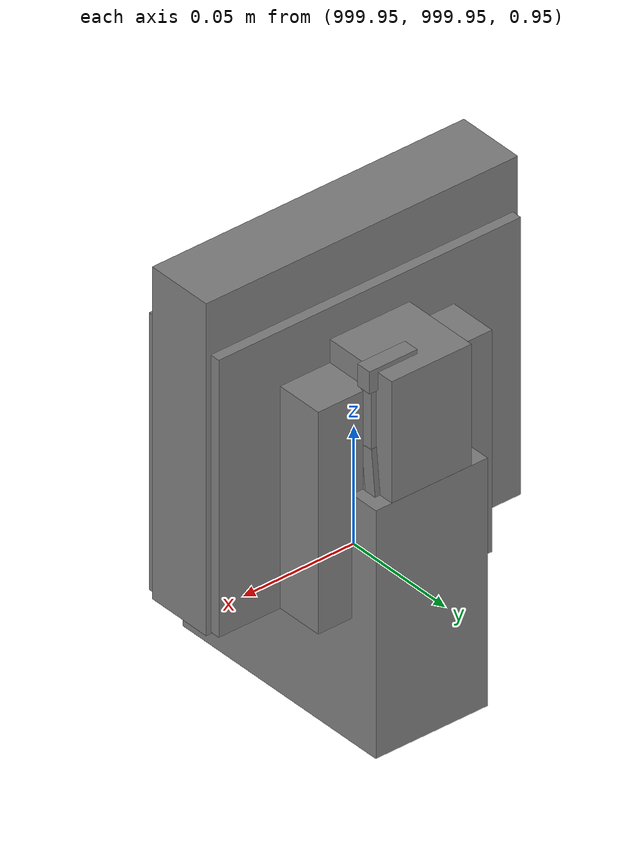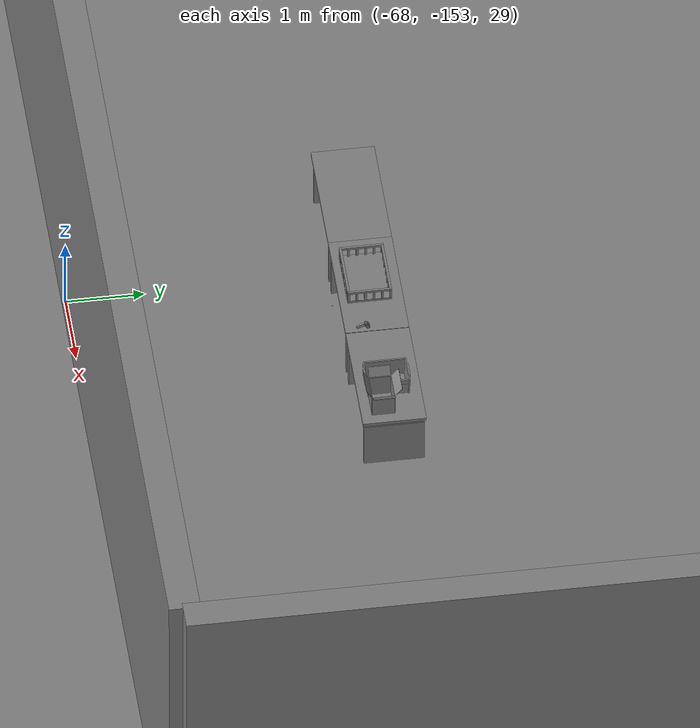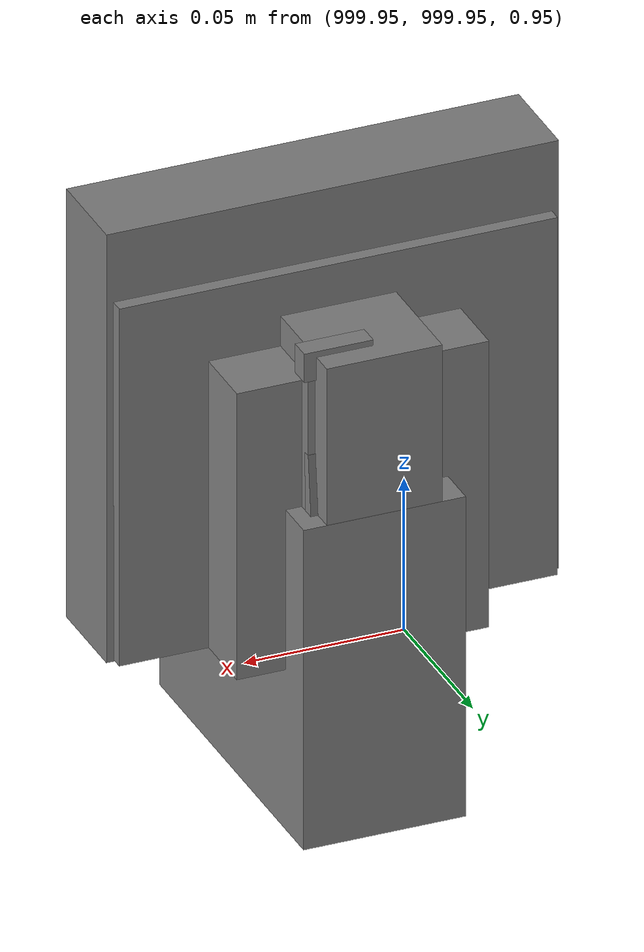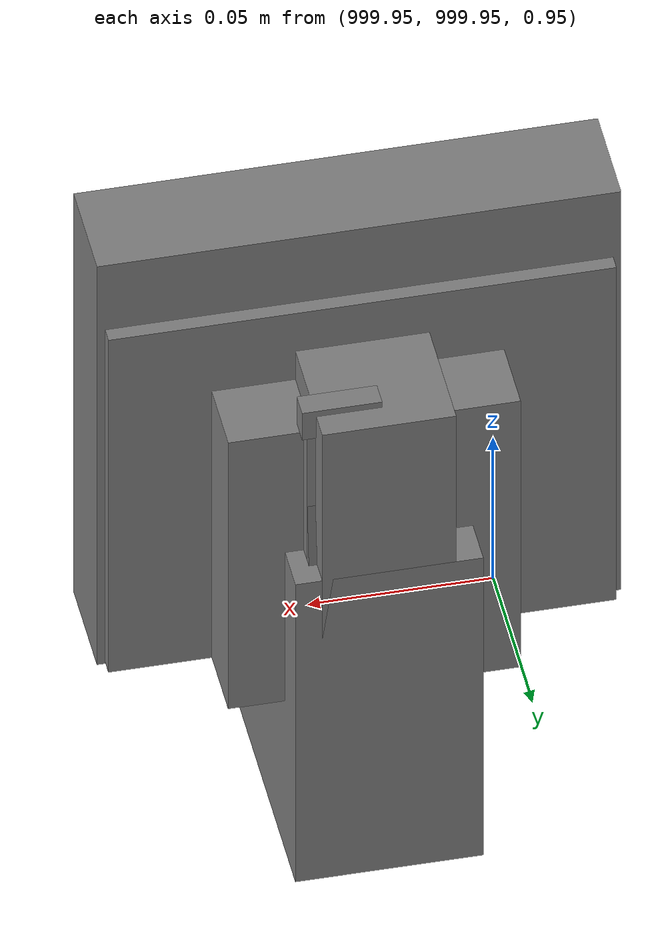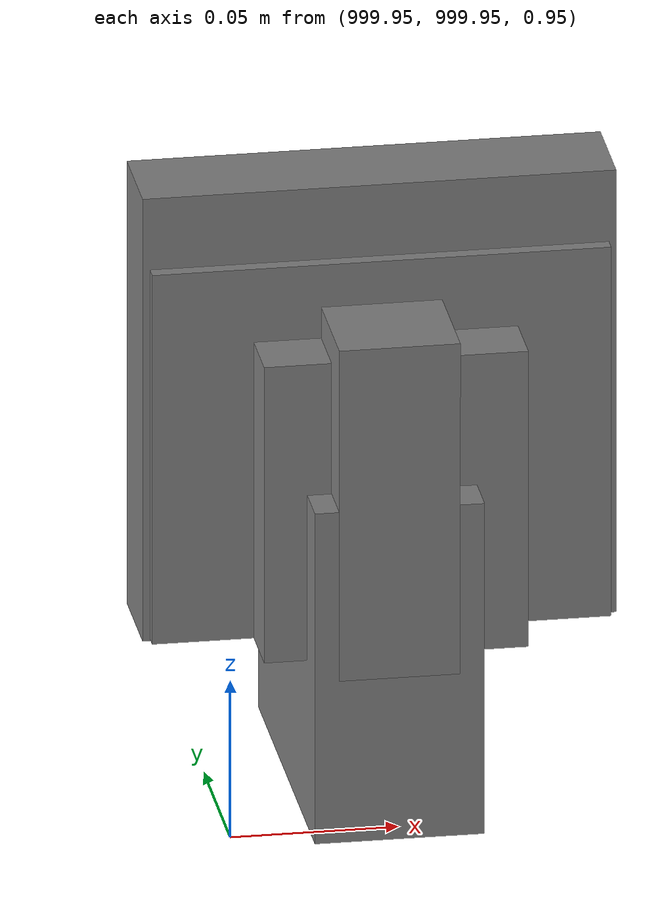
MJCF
<mujoco>
    <option gravity="0.000000000 0.000000000 -9.810000420" timestep="0.0049999999" integrator="implicitfast" density="1.225" viscosity="1.8000001e-05" noslip_iterations="10" iterations="100" sdf_iterations="50">
        <flag multiccd="disable"/>
    </option>
    <size memory="1000M"/>
    <compiler coordinate="local"/>
    <worldbody>
        <light cutoff="30" pos="0 1 1" dir="0 -1 -2"/>
        <light cutoff="30" pos="0 -1 1" dir="0 1 -2"/>
        <body pos="1000.000000000 999.999938965 1.000000000" euler="0.000000000 0.000000000 180.000000000" name="openloong_gripper_2f85_fix_base_usda_intelcore_i5">
            <geom contype="1" conaffinity="1" density="1000" type="box" material="" rgba="0.500000000 0.500000000 0.500000000 1.000000000" solimp="0.899999976 0.949999988 0.001000000" friction="1.000000000 0.005000000 0.000100000" solref="0.020000000 1.000000000" margin="0" condim="3" group="0" pos="0.000000000 0.000000000 0.051722717" quat="0.707106709 0.000000000 0.000000000 -0.707106769" size="0.052800000 0.018080002 0.052800000" name="openloong_gripper_2f85_fix_base_usda_geom_0CA234E5_F41A_475A_BD38_7F911A68C3A3"/>
            <freejoint name="openloong_gripper_2f85_fix_base_usda_intelcore_i5_joint"/>
            <site size="0.005000000 0.005000000 0.005000000" rgba="0.500000000 0.500000000 0.500000000 1.000000000" pos="0.000000000 0.000000000 0.000000000" quat="0.999961913 0.008726534 0.000000000 0.000000000" group="0" type="sphere" name="openloong_gripper_2f85_fix_base_usda_intelcore_i5site"/>
        </body>
        <body pos="1000.000000000 1000.000000000 1.000000000" euler="0.000000000 0.000000000 180.000000000" name="openloong_gripper_2f85_fix_base_usda_wifi_box">
            <geom contype="1" conaffinity="1" density="1000" type="box" material="" rgba="0.500000000 0.500000000 0.500000000 1.000000000" solimp="0.899999976 0.949999988 0.001000000" friction="1.000000000 0.005000000 0.000100000" solref="0.020000000 1.000000000" margin="0" condim="3" group="0" pos="0.000000000 0.000000000 0.058978677" quat="0.000000000 0.000000047 0.000000000 1.000000000" size="0.068499997 0.018999999 0.059000000" name="openloong_gripper_2f85_fix_base_usda_geom_7E314B6A_33EA_42BB_8722_634A83ABF571"/>
            <freejoint name="openloong_gripper_2f85_fix_base_usda_wifi_box_joint"/>
            <site size="0.005000000 0.005000000 0.005000000" rgba="0.500000000 0.500000000 0.500000000 1.000000000" pos="0.000000000 0.000000000 0.000000000" quat="0.999961913 0.008726500 0.000000000 0.000000000" group="0" type="sphere" name="openloong_gripper_2f85_fix_base_usda_wifi_boxsite"/>
        </body>
        <body pos="1000.000000000 1000.000000000 1.000000000" euler="0.000011953 0.000005123 -179.999984741" name="openloong_gripper_2f85_fix_base_usda_intel_box">
            <geom contype="1" conaffinity="1" density="1000" type="box" material="" rgba="0.500000000 0.500000000 0.500000000 1.000000000" solimp="0.899999976 0.949999988 0.001000000" friction="1.000000000 0.005000000 0.000100000" solref="0.020000000 1.000000000" margin="0" condim="3" group="0" pos="0.000000000 -0.000067139 0.000082284" quat="0.707106709 0.000000225 0.000000253 0.707106650" size="0.052800003 0.025300000 0.052800003" name="openloong_gripper_2f85_fix_base_usda_geom_5E9C9C04_A2B1_4823_99C6_58AB7F14CD35"/>
            <freejoint name="openloong_gripper_2f85_fix_base_usda_intel_box_joint"/>
            <site size="0.005000000 0.005000000 0.005000000" rgba="0.500000000 0.500000000 0.500000000 1.000000000" pos="0.000000000 0.000000000 0.000000000" quat="0.999961913 0.008726500 0.000000000 0.000000000" group="0" type="sphere" name="openloong_gripper_2f85_fix_base_usda_intel_boxsite"/>
        </body>
        <body pos="-66.082733154 -148.909179688 31.167428970" euler="43.441741943 -2.669498920 177.980545044" mocap="true" name="spotlight1_SpotLight"/>
        <body pos="1000.000000000 1000.000000000 1.000000000" euler="0.000000000 0.000000000 180.000000000" name="openloong_gripper_2f85_fix_base_usda_cpu_fan">
            <geom contype="1" conaffinity="1" density="1000" type="box" material="" rgba="0.500000000 0.500000000 0.500000000 1.000000000" solimp="0.899999976 0.949999988 0.001000000" friction="1.000000000 0.005000000 0.000100000" solref="0.020000000 1.000000000" margin="0" condim="3" group="0" pos="0.000000000 0.000000000 0.070034981" quat="0.000000000 0.000000000 0.000000000 1.000000000" size="0.070700005 0.014699999 0.070700005" name="openloong_gripper_2f85_fix_base_usda_geom_D2012469_A4AE_4339_8D92_33023DA6D9E1"/>
            <freejoint name="openloong_gripper_2f85_fix_base_usda_cpu_fan_joint"/>
            <site size="0.005000000 0.005000000 0.005000000" rgba="0.500000000 0.500000000 0.500000000 1.000000000" pos="0.000000000 0.000000000 0.000000000" quat="0.999961913 0.008726535 0.000000000 0.000000000" group="0" type="sphere" name="openloong_gripper_2f85_fix_base_usda_cpu_fancsite"/>
        </body>
        <body pos="-66.360336304 -149.707031250 31.162693024" euler="-141.184906006 76.980110168 -139.345306396" mocap="true" name="spotlight3_SpotLight"/>
        <body pos="1000.000000000 1000.000000000 1.000000000" euler="0.000000000 0.000000000 180.000000000" name="openloong_gripper_2f85_fix_base_usda_battery_01">
            <geom contype="1" conaffinity="1" density="1000" type="box" material="" rgba="0.500000000 0.500000000 0.500000000 1.000000000" solimp="0.899999976 0.949999988 0.001000000" friction="1.000000000 0.005000000 0.000100000" solref="0.020000000 1.000000000" margin="0" condim="3" group="0" pos="-0.011123657 -0.041940309 0.101691343" quat="1.000000000 0.000000000 0.000000000 0.000000000" size="0.010800000 0.003375000 0.004725000" name="openloong_gripper_2f85_fix_base_usda_geom_9D352738_4CEE_472F_ABFF_AEF2A160CD5B"/>
            <geom contype="1" conaffinity="1" density="1000" type="box" material="" rgba="0.500000000 0.500000000 0.500000000 1.000000000" solimp="0.899999976 0.949999988 0.001000000" friction="1.000000000 0.005000000 0.000100000" solref="0.020000000 1.000000000" margin="0" condim="3" group="0" pos="-0.010876465 -0.044247437 0.047066893" quat="0.998702705 -0.050920475 0.000000000 0.000000000" size="0.009450001 0.002700000 0.024975000" name="openloong_gripper_2f85_fix_base_usda_geom_D50CD230_E651_468E_BF7E_E59C4997CC2E"/>
            <geom contype="1" conaffinity="1" density="1000" type="box" material="" rgba="0.500000000 0.500000000 0.500000000 1.000000000" solimp="0.899999976 0.949999988 0.001000000" friction="1.000000000 0.005000000 0.000100000" solref="0.020000000 1.000000000" margin="0" condim="3" group="0" pos="-0.001235962 -0.000659180 0.047381196" quat="1.000000000 0.000000000 0.000000000 0.000000000" size="0.039420001 0.039150000 0.047250003" name="openloong_gripper_2f85_fix_base_usda_geom_884D21B9_B086_475F_AD72_0A5124034870"/>
            <geom contype="1" conaffinity="1" density="1000" type="box" material="" rgba="0.500000000 0.500000000 0.500000000 1.000000000" solimp="0.899999976 0.949999988 0.001000000" friction="1.000000000 0.005000000 0.000100000" solref="0.020000000 1.000000000" margin="0" condim="3" group="0" pos="-0.010876465 -0.039138794 0.009851727" quat="1.000000000 0.000000000 0.000000000 0.000000000" size="0.009450001 0.010800000 0.013500000" name="openloong_gripper_2f85_fix_base_usda_geom_C865CA32_054E_4EF9_9FBE_117996ADBD2E"/>
            <geom contype="1" conaffinity="1" density="1000" type="box" material="" rgba="0.500000000 0.500000000 0.500000000 1.000000000" solimp="0.899999976 0.949999988 0.001000000" friction="1.000000000 0.005000000 0.000100000" solref="0.020000000 1.000000000" margin="0" condim="3" group="0" pos="-0.010876465 -0.041528322 0.071508206" quat="1.000000000 0.000000000 0.000000000 0.000000000" size="0.009450001 0.002700000 0.027000001" name="openloong_gripper_2f85_fix_base_usda_geom_E73DF1A6_1E7A_4EE6_AAF3_A4883393D1C0"/>
            <freejoint name="openloong_gripper_2f85_fix_base_usda_battery_01_joint"/>
            <site size="0.005000000 0.005000000 0.005000000" rgba="0.500000000 0.500000000 0.500000000 1.000000000" pos="0.000000000 0.000000000 0.000000000" quat="0.999961913 0.008726500 0.000000000 0.000000000" group="0" type="sphere" name="openloong_gripper_2f85_fix_base_usda_battery_01site"/>
        </body>
        <body pos="-65.905738831 -148.964523315 31.168050766" euler="-44.582569122 -87.226753235 71.026283264" mocap="true" name="spotlight4_SpotLight"/>
        <body pos="-64.866622925 -149.383972168 30.183746338" euler="89.999984741 89.999946594 0.000000000" name="openloong_gripper_2f85_fix_base_usda_bluebox_01">
            <geom contype="1" conaffinity="1" density="1000" type="box" material="" rgba="0.500000000 0.500000000 0.500000000 1.000000000" solimp="0.899999976 0.949999988 0.001000000" friction="1.000000000 0.005000000 0.000100000" solref="0.020000000 1.000000000" margin="0" condim="3" group="0" pos="0.276580811 0.187225342 0.000068665" quat="0.707106948 0.000077471 0.707106352 0.000077486" size="0.100000001 0.057999998 0.010000000" name="openloong_gripper_2f85_fix_base_usda_geom_D59AB75D_991E_443E_9E18_68E7BF9CFC5A"/>
            <geom contype="1" conaffinity="1" density="1000" type="box" material="" rgba="0.500000000 0.500000000 0.500000000 1.000000000" solimp="0.899999976 0.949999988 0.001000000" friction="1.000000000 0.005000000 0.000100000" solref="0.020000000 1.000000000" margin="0" condim="3" group="0" pos="0.000000000 0.002883911 0.000000000" quat="0.999999881 0.000000000 0.000000000 0.000000000" size="0.254000008 0.003000000 0.172000006" name="openloong_gripper_2f85_fix_base_usda_geom_B5E82038_BDAD_4D1A_B3E2_32A0A270171E"/>
            <geom contype="1" conaffinity="1" density="1000" type="box" material="" rgba="0.500000000 0.500000000 0.500000000 1.000000000" solimp="0.899999976 0.949999988 0.001000000" friction="1.000000000 0.005000000 0.000100000" solref="0.020000000 1.000000000" margin="0" condim="3" group="0" pos="0.000000000 0.124874115 0.173484802" quat="0.999796331 0.020176515 -0.000000015 0.000000030" size="0.259999990 0.119999997 0.007000000" name="openloong_gripper_2f85_fix_base_usda_geom_DB5F0769_BB6B_4F9D_8D14_524B31B46631"/>
            <geom contype="1" conaffinity="1" density="1000" type="box" material="" rgba="0.500000000 0.500000000 0.500000000 1.000000000" solimp="0.899999976 0.949999988 0.001000000" friction="1.000000000 0.005000000 0.000100000" solref="0.020000000 1.000000000" margin="0" condim="3" group="0" pos="0.000000000 0.124874115 -0.173469543" quat="0.999796331 -0.020176545 -0.000000015 0.000000000" size="0.259999990 0.119999997 0.007000000" name="openloong_gripper_2f85_fix_base_usda_geom_1C3CF035_0617_4E71_8DD4_C17FFC7F6C1E"/>
            <geom contype="1" conaffinity="1" density="1000" type="box" material="" rgba="0.500000000 0.500000000 0.500000000 1.000000000" solimp="0.899999976 0.949999988 0.001000000" friction="1.000000000 0.005000000 0.000100000" solref="0.020000000 1.000000000" margin="0" condim="3" group="0" pos="0.000000000 0.214008331 0.188980103" quat="0.999912977 0.013176724 0.000000015 0.000000000" size="0.259999990 0.029999999 0.012500000" name="openloong_gripper_2f85_fix_base_usda_geom_8F4D859D_1F08_48B4_8289_B17C10BB6151"/>
            <geom contype="1" conaffinity="1" density="1000" type="box" material="" rgba="0.500000000 0.500000000 0.500000000 1.000000000" solimp="0.899999976 0.949999988 0.001000000" friction="1.000000000 0.005000000 0.000100000" solref="0.020000000 1.000000000" margin="0" condim="3" group="0" pos="-0.258361816 0.125289917 0.001876831" quat="0.702796936 -0.020792112 0.710783124 0.020769298" size="0.189999998 0.119999997 0.009000000" name="openloong_gripper_2f85_fix_base_usda_geom_62F4425B_7826_4F3D_9F7E_8AD190896DF9"/>
            <geom contype="1" conaffinity="1" density="1000" type="box" material="" rgba="0.500000000 0.500000000 0.500000000 1.000000000" solimp="0.899999976 0.949999988 0.001000000" friction="1.000000000 0.005000000 0.000100000" solref="0.020000000 1.000000000" margin="0" condim="3" group="0" pos="0.000000000 0.214008331 -0.188980103" quat="0.999912977 -0.013176769 0.000000030 0.000000015" size="0.259999990 0.029999999 0.012500000" name="openloong_gripper_2f85_fix_base_usda_geom_BDE3BCB8_8F4F_4D67_8C96_4F3D0A38E3E5"/>
            <geom contype="1" conaffinity="1" density="1000" type="box" material="" rgba="0.500000000 0.500000000 0.500000000 1.000000000" solimp="0.899999976 0.949999988 0.001000000" friction="1.000000000 0.005000000 0.000100000" solref="0.020000000 1.000000000" margin="0" condim="3" group="0" pos="-0.276611328 0.187225342 0.000068665" quat="0.707106650 0.000077441 0.707106709 0.000077456" size="0.100000001 0.057999998 0.010000000" name="openloong_gripper_2f85_fix_base_usda_geom_7E03A15B_4F0B_4AAC_8588_B3F33314D37B"/>
            <geom contype="1" conaffinity="1" density="1000" type="box" material="" rgba="0.500000000 0.500000000 0.500000000 1.000000000" solimp="0.899999976 0.949999988 0.001000000" friction="1.000000000 0.005000000 0.000100000" solref="0.020000000 1.000000000" margin="0" condim="3" group="0" pos="0.258331299 0.125289917 0.001876831" quat="0.702851415 0.018856421 0.710823774 -0.019329369" size="0.189999998 0.119999997 0.009000000" name="openloong_gripper_2f85_fix_base_usda_geom_DF117BD3_4C4A_42D1_9D2D_AA779B7A2D30"/>
            <freejoint name="openloong_gripper_2f85_fix_base_usda_bluebox_01_joint"/>
            <site size="0.005000000 0.005000000 0.005000000" rgba="0.500000000 0.500000000 0.500000000 1.000000000" pos="0.000000000 0.000000000 0.000000000" quat="0.999961913 0.008726534 0.000000000 0.000000000" group="0" type="sphere" name="openloong_gripper_2f85_fix_base_usda_bluebox_01site"/>
        </body>
        <body pos="-64.496299744 -149.491867065 30.235729218" euler="0.000000000 0.000000000 89.999946594" name="openloong_gripper_2f85_fix_base_usda_cardboardbox_01">
            <geom contype="1" conaffinity="1" density="1000" type="box" material="" rgba="0.500000000 0.500000000 0.500000000 1.000000000" solimp="0.899999976 0.949999988 0.001000000" friction="1.000000000 0.005000000 0.000100000" solref="0.020000000 1.000000000" margin="0" condim="3" group="0" pos="-0.003166199 -0.004086494 0.005052090" quat="1.000000000 0.000000000 0.000000000 0.000000000" size="0.142499998 0.177500010 0.005000000" name="openloong_gripper_2f85_fix_base_usda_geom_4B6765B3_7551_4500_8A34_B86FDFF70BB5"/>
            <geom contype="1" conaffinity="1" density="1000" type="box" material="" rgba="0.500000000 0.500000000 0.500000000 1.000000000" solimp="0.899999976 0.949999988 0.001000000" friction="1.000000000 0.005000000 0.000100000" solref="0.020000000 1.000000000" margin="0" condim="3" group="0" pos="-0.003166199 0.170316696 0.150570869" quat="1.000000000 0.000000000 0.000000000 0.000000000" size="0.142499998 0.005000000 0.149999991" name="openloong_gripper_2f85_fix_base_usda_geom_752D8175_A060_4625_9749_29903C245767"/>
            <geom contype="1" conaffinity="1" density="1000" type="box" material="" rgba="0.500000000 0.500000000 0.500000000 1.000000000" solimp="0.899999976 0.949999988 0.001000000" friction="1.000000000 0.005000000 0.000100000" solref="0.020000000 1.000000000" margin="0" condim="3" group="0" pos="-0.147399902 -0.005307198 0.150570869" quat="1.000000000 0.000000000 0.000000000 0.000000000" size="0.005000000 0.177500010 0.149999991" name="openloong_gripper_2f85_fix_base_usda_geom_FCB13856_C8D6_4E63_9ABE_BB7DBB2B54E7"/>
            <geom contype="1" conaffinity="1" density="1000" type="box" material="" rgba="0.500000000 0.500000000 0.500000000 1.000000000" solimp="0.899999976 0.949999988 0.001000000" friction="1.000000000 0.005000000 0.000100000" solref="0.020000000 1.000000000" margin="0" condim="3" group="0" pos="0.140275955 -0.005307198 0.150570869" quat="1.000000000 0.000000000 0.000000000 0.000000000" size="0.005000000 0.177500010 0.149999991" name="openloong_gripper_2f85_fix_base_usda_geom_6F590870_7504_47E8_B191_F0B689BB53C3"/>
            <geom contype="1" conaffinity="1" density="1000" type="box" material="" rgba="0.500000000 0.500000000 0.500000000 1.000000000" solimp="0.899999976 0.949999988 0.001000000" friction="1.000000000 0.005000000 0.000100000" solref="0.020000000 1.000000000" margin="0" condim="3" group="0" pos="-0.003166199 -0.181550980 0.150570869" quat="1.000000000 0.000000000 0.000000000 0.000000000" size="0.142499998 0.005000000 0.149999991" name="openloong_gripper_2f85_fix_base_usda_geom_2D4327D7_108A_43A7_8B00_1AA9DC5DA4F5"/>
            <freejoint name="openloong_gripper_2f85_fix_base_usda_cardboardbox_01_joint"/>
            <site size="0.005000000 0.005000000 0.005000000" rgba="0.500000000 0.500000000 0.500000000 1.000000000" pos="0.000000000 0.000000000 0.000000000" quat="0.999961913 0.008726535 0.000000000 0.000000000" group="0" type="sphere" name="openloong_gripper_2f85_fix_base_usda_site_843969DD_1E06_4F79_9892_E038D036EB73"/>
            <body pos="0.139160156 -0.004048347 0.301930904" euler="-179.999954224 49.383502960 179.999954224" name="openloong_gripper_2f85_fix_base_usda_A1_006">
                <geom contype="1" conaffinity="1" density="1000" type="box" material="" rgba="0.500000000 0.500000000 0.500000000 1.000000000" solimp="0.899999976 0.949999988 0.001000000" friction="1.000000000 0.005000000 0.000100000" solref="0.020000000 1.000000000" margin="0" condim="3" group="0" pos="-0.071587563 0.000009537 0.001745224" quat="0.999999881 0.000000000 0.000000000 0.000000000" size="0.071249999 0.179999992 0.002500000" name="openloong_gripper_2f85_fix_base_usda_geom_BF8CDB38_306F_4639_BF15_68880B4D5683"/>
                <joint armature="0" stiffness="0.07" damping="0.0099999998" axis="0.000000 1.000000 0.000000" type="hinge" name="openloong_gripper_2f85_fix_base_usda_A1_006"/>
            </body>
            <body pos="-0.145902634 -0.004086494 0.301938057" euler="-180.000000000 -60.000011444 -180.000000000" name="openloong_gripper_2f85_fix_base_usda_A2_006">
                <geom contype="1" conaffinity="1" density="1000" type="box" material="" rgba="0.500000000 0.500000000 0.500000000 1.000000000" solimp="0.899999976 0.949999988 0.001000000" friction="1.000000000 0.005000000 0.000100000" solref="0.020000000 1.000000000" margin="0" condim="3" group="0" pos="0.071268082 0.000009537 0.002717972" quat="0.000002921 0.000000000 -0.000000030 0.999999881" size="0.071249999 0.179999992 0.002500000" name="openloong_gripper_2f85_fix_base_usda_geom_CD7CB705_66A7_4ED7_8023_8A07710C82BA"/>
                <joint armature="0" stiffness="0.07" damping="0.0099999998" axis="0.000000 1.000000 0.000000" type="hinge" name="openloong_gripper_2f85_fix_base_usda_A2_006"/>
            </body>
            <body pos="-0.003385544 0.175991058 0.301930904" euler="-125.858116150 -0.000004561 0.000002331" name="openloong_gripper_2f85_fix_base_usda_B2_006">
                <geom contype="1" conaffinity="1" density="1000" type="box" material="" rgba="0.500000000 0.500000000 0.500000000 1.000000000" solimp="0.899999976 0.949999988 0.001000000" friction="1.000000000 0.005000000 0.000100000" solref="0.020000000 1.000000000" margin="0" condim="3" group="0" pos="0.000009537 -0.070939064 -0.002470016" quat="0.999614120 0.027776197 -0.000000015 0.000000030" size="0.137500003 0.064999998 0.005000000" name="openloong_gripper_2f85_fix_base_usda_geom_B08966AF_1272_4441_8111_4FD069B6EAF3"/>
                <joint armature="0" stiffness="0.07" damping="0.0099999998" axis="1.000000 0.000000 0.000000" type="hinge" name="openloong_gripper_2f85_fix_base_usda_B2_006"/>
            </body>
            <body pos="-0.003385544 -0.184140205 0.301938057" euler="147.805557251 0.000000000 0.000000000" name="openloong_gripper_2f85_fix_base_usda_B1_006">
                <geom contype="1" conaffinity="1" density="1000" type="box" material="" rgba="0.500000000 0.500000000 0.500000000 1.000000000" solimp="0.899999976 0.949999988 0.001000000" friction="1.000000000 0.005000000 0.000100000" solref="0.020000000 1.000000000" margin="0" condim="3" group="0" pos="-0.000028610 0.070202351 -0.002703667" quat="0.999614179 -0.027776167 0.000000000 0.000000000" size="0.137500003 0.064999998 0.005000000" name="openloong_gripper_2f85_fix_base_usda_geom_98266091_5C8C_49A0_943F_A57CFF3ACFF2"/>
                <joint armature="0" stiffness="0.07" damping="0.0099999998" axis="1.000000 0.000000 0.000000" type="hinge" name="openloong_gripper_2f85_fix_base_usda_B1_006"/>
            </body>
        </body>
        <body pos="-65.882858276 -149.481979370 30.229999542" euler="-64.487716675 0.000000000 0.000000000" name="openloong_gripper_2f85_fix_base_usda_Barcode">
            <geom contype="1" conaffinity="1" density="1000" type="box" material="" rgba="0.500000000 0.500000000 0.500000000 1.000000000" solimp="0.899999976 0.949999988 0.001000000" friction="1.000000000 0.005000000 0.000100000" solref="0.020000000 1.000000000" margin="0" condim="3" group="0" pos="0.000000000 0.013038635 0.001419067" quat="0.000000000 0.000000000 0.000000000 1.000000119" size="0.034000002 0.010000000 0.017999999" name="openloong_gripper_2f85_fix_base_usda_geom_33E08701_7BE4_456F_A259_387CC99A2C1B"/>
            <geom contype="1" conaffinity="1" density="1000" type="box" material="" rgba="0.500000000 0.500000000 0.500000000 1.000000000" solimp="0.899999976 0.949999988 0.001000000" friction="1.000000000 0.005000000 0.000100000" solref="0.020000000 1.000000000" margin="0" condim="3" group="0" pos="0.000000000 -0.035301208 -0.007095337" quat="0.000000000 0.000000000 -0.043619365 0.999048233" size="0.028999999 0.010000000 0.020000000" name="openloong_gripper_2f85_fix_base_usda_geom_6ED18AED_1230_4FD3_97E0_DD7A8768BCC5"/>
            <geom contype="1" conaffinity="1" density="1000" type="box" material="" rgba="0.500000000 0.500000000 0.500000000 1.000000000" solimp="0.899999976 0.949999988 0.001000000" friction="1.000000000 0.005000000 0.000100000" solref="0.020000000 1.000000000" margin="0" condim="3" group="0" pos="0.000000000 -0.043411255 -0.011749268" quat="0.922262907 0.386563420 0.000000000 0.000000000" size="0.026000001 0.010000000 0.020000000" name="openloong_gripper_2f85_fix_base_usda_geom_3B95A136_8B51_4CFB_8FED_AD4BCFBF0C52"/>
            <geom contype="1" conaffinity="1" density="1000" type="box" material="" rgba="0.500000000 0.500000000 0.500000000 1.000000000" solimp="0.899999976 0.949999988 0.001000000" friction="1.000000000 0.005000000 0.000100000" solref="0.020000000 1.000000000" margin="0" condim="3" group="0" pos="0.000000000 -0.016967773 -0.031860352" quat="0.000000000 0.000000000 0.000000000 1.000000119" size="0.008000000 0.010000000 0.013000000" name="openloong_gripper_2f85_fix_base_usda_geom_5D553358_568A_4DA1_9620_1D6D5A6CEDC5"/>
            <geom contype="1" conaffinity="1" density="1000" type="box" material="" rgba="0.500000000 0.500000000 0.500000000 1.000000000" solimp="0.899999976 0.949999988 0.001000000" friction="1.000000000 0.005000000 0.000100000" solref="0.020000000 1.000000000" margin="0" condim="3" group="0" pos="0.000000000 -0.001869202 0.000312805" quat="0.953716993 0.300705761 0.000000000 0.000000000" size="0.032000002 0.010000000 0.018999999" name="openloong_gripper_2f85_fix_base_usda_geom_071A1CEE_DD93_4CA5_9C8F_EBFD719D3BDF"/>
            <geom contype="1" conaffinity="1" density="1000" type="box" material="" rgba="0.500000000 0.500000000 0.500000000 1.000000000" solimp="0.899999976 0.949999988 0.001000000" friction="1.000000000 0.005000000 0.000100000" solref="0.020000000 1.000000000" margin="0" condim="3" group="0" pos="0.000000000 -0.019531250 -0.003173828" quat="0.953716993 0.300705761 0.000000000 0.000000000" size="0.030999999 0.010000000 0.020000000" name="openloong_gripper_2f85_fix_base_usda_geom_3646A74D_F89C_4F61_B88F_0CDEB391A34F"/>
            <geom contype="1" conaffinity="1" density="1000" type="box" material="" rgba="0.500000000 0.500000000 0.500000000 1.000000000" solimp="0.899999976 0.949999988 0.001000000" friction="1.000000000 0.005000000 0.000100000" solref="0.020000000 1.000000000" margin="0" condim="3" group="0" pos="0.000000000 -0.035301208 -0.007095337" quat="0.953716993 0.300705761 0.000000000 0.000000000" size="0.028999999 0.010000000 0.020000000" name="openloong_gripper_2f85_fix_base_usda_geom_EA6A41AE_8016_4DF0_AD01_6D7F6FE02544"/>
            <geom contype="1" conaffinity="1" density="1000" type="box" material="" rgba="0.500000000 0.500000000 0.500000000 1.000000000" solimp="0.899999976 0.949999988 0.001000000" friction="1.000000000 0.005000000 0.000100000" solref="0.020000000 1.000000000" margin="0" condim="3" group="0" pos="0.000000000 -0.042617798 -0.071121216" quat="0.000000000 0.000000000 0.000000000 1.000000119" size="0.013000000 0.021000000 0.059999999" name="openloong_gripper_2f85_fix_base_usda_geom_D5409CFF_DC83_4AFB_A916_4BBEF1C71DC5"/>
            <freejoint name="openloong_gripper_2f85_fix_base_usda_Barcode_joint"/>
            <site size="0.005000000 0.005000000 0.005000000" rgba="0.500000000 0.500000000 0.500000000 1.000000000" pos="0.000000000 0.000000000 0.000000000" quat="1.000000000 0.000000000 0.000000000 0.000000000" group="0" type="sphere" name="openloong_gripper_2f85_fix_base_usda_Barcode_site"/>
        </body>
        <body pos="-66.745018005 -149.392349243 30.184000015" euler="0.000000000 0.000000000 89.999946594" name="[22333440653386]_Basket_01">
            <geom contype="1" conaffinity="1" density="1000" type="box" material="" rgba="0.500000000 0.500000000 0.500000000 1.000000000" solimp="0.899999976 0.949999988 0.001000000" friction="1.000000000 0.005000000 0.000100000" solref="0.020000000 1.000000000" margin="0" condim="3" group="0" pos="-0.052425385 0.389207840 0.089787483" quat="0.707107008 0.000000000 0.000000000 0.707106411" size="0.014249999 0.014249999 0.059999999" name="[22333440653386]_geom_DDCD6CF8_9ED2_42A9_A080_BB86BCDE7114"/>
            <geom contype="1" conaffinity="1" density="1000" type="box" material="" rgba="0.500000000 0.500000000 0.500000000 1.000000000" solimp="0.899999976 0.949999988 0.001000000" friction="1.000000000 0.005000000 0.000100000" solref="0.020000000 1.000000000" margin="0" condim="3" group="0" pos="0.264015198 -0.133043289 0.089787483" quat="0.707107008 0.000000000 0.000000000 0.707106411" size="0.014249999 0.014249999 0.059999999" name="[22333440653386]_geom_9FC30192_20D7_458E_B782_A18C5377B431"/>
            <geom contype="1" conaffinity="1" density="1000" type="box" material="" rgba="0.500000000 0.500000000 0.500000000 1.000000000" solimp="0.899999976 0.949999988 0.001000000" friction="1.000000000 0.005000000 0.000100000" solref="0.020000000 1.000000000" margin="0" condim="3" group="0" pos="-0.264015198 -0.265548706 0.089793205" quat="0.707107008 0.000000000 0.000000000 0.707106411" size="0.014249999 0.014249999 0.059999999" name="[22333440653386]_geom_62D5B2F3_B2B4_4A95_97C3_8D3BEA1DC605"/>
            <geom contype="1" conaffinity="1" density="1000" type="box" material="" rgba="0.500000000 0.500000000 0.500000000 1.000000000" solimp="0.899999976 0.949999988 0.001000000" friction="1.000000000 0.005000000 0.000100000" solref="0.020000000 1.000000000" margin="0" condim="3" group="0" pos="-0.160263062 -0.389322281 0.089793205" quat="0.707107008 0.000000000 0.000000000 0.707106411" size="0.014249999 0.014249999 0.059999999" name="[22333440653386]_geom_7947CF97_E1FB_4BBD_816A_BB8CA7712197"/>
            <geom contype="1" conaffinity="1" density="1000" type="box" material="" rgba="0.500000000 0.500000000 0.500000000 1.000000000" solimp="0.899999976 0.949999988 0.001000000" friction="1.000000000 0.005000000 0.000100000" solref="0.020000000 1.000000000" margin="0" condim="3" group="0" pos="0.162265778 -0.389322281 0.089787483" quat="0.707107008 0.000000000 0.000000000 0.707106411" size="0.014249999 0.014249999 0.059999999" name="[22333440653386]_geom_16102AD0_799C_48FB_9652_6B8ACF69F4DE"/>
            <geom contype="1" conaffinity="1" density="1000" type="box" material="" rgba="0.500000000 0.500000000 0.500000000 1.000000000" solimp="0.899999976 0.949999988 0.001000000" friction="1.000000000 0.005000000 0.000100000" solref="0.020000000 1.000000000" margin="0" condim="3" group="0" pos="0.264015198 0.389207840 0.089787483" quat="0.707107008 0.000000000 0.000000000 0.707106411" size="0.014249999 0.014249999 0.059999999" name="[22333440653386]_geom_789BF4B2_EADA_47B1_B3F0_DB17A23C9AE7"/>
            <geom contype="1" conaffinity="1" density="1000" type="box" material="" rgba="0.500000000 0.500000000 0.500000000 1.000000000" solimp="0.899999976 0.949999988 0.001000000" friction="1.000000000 0.005000000 0.000100000" solref="0.020000000 1.000000000" margin="0" condim="3" group="0" pos="-0.264015198 -0.133043289 0.089793205" quat="0.707107008 0.000000000 0.000000000 0.707106411" size="0.014249999 0.014249999 0.059999999" name="[22333440653386]_geom_D9B8B3ED_59EF_4BCB_8FE3_699E9D63BDC1"/>
            <geom contype="1" conaffinity="1" density="1000" type="box" material="" rgba="0.500000000 0.500000000 0.500000000 1.000000000" solimp="0.899999976 0.949999988 0.001000000" friction="1.000000000 0.005000000 0.000100000" solref="0.020000000 1.000000000" margin="0" condim="3" group="0" pos="-0.264026642 0.269256592 0.089793205" quat="0.707107008 0.000000000 0.000000000 0.707106411" size="0.014249999 0.014249999 0.059999999" name="[22333440653386]_geom_05DD4015_5B51_40E2_B0FB_85ED25D5D06B"/>
            <geom contype="1" conaffinity="1" density="1000" type="box" material="" rgba="0.500000000 0.500000000 0.500000000 1.000000000" solimp="0.899999976 0.949999988 0.001000000" friction="1.000000000 0.005000000 0.000100000" solref="0.020000000 1.000000000" margin="0" condim="3" group="0" pos="0.054462433 0.389207840 0.089787483" quat="0.707107008 0.000000000 0.000000000 0.707106411" size="0.014249999 0.014249999 0.059999999" name="[22333440653386]_geom_3E15D6B2_13A5_4781_9FE9_36AC5851112A"/>
            <geom contype="1" conaffinity="1" density="1000" type="box" material="" rgba="0.500000000 0.500000000 0.500000000 1.000000000" solimp="0.899999976 0.949999988 0.001000000" friction="1.000000000 0.005000000 0.000100000" solref="0.020000000 1.000000000" margin="0" condim="3" group="0" pos="0.054462433 -0.389322281 0.089787483" quat="0.707107008 0.000000000 0.000000000 0.707106411" size="0.014249999 0.014249999 0.059999999" name="[22333440653386]_geom_A379D02E_8355_4A9B_B5F1_43EC6899FE4A"/>
            <geom contype="1" conaffinity="1" density="1000" type="box" material="" rgba="0.500000000 0.500000000 0.500000000 1.000000000" solimp="0.899999976 0.949999988 0.001000000" friction="1.000000000 0.005000000 0.000100000" solref="0.020000000 1.000000000" margin="0" condim="3" group="0" pos="0.264015198 0.269256592 0.089793205" quat="0.707107008 0.000000000 0.000000000 0.707106411" size="0.014249999 0.014249999 0.059999999" name="[22333440653386]_geom_4318A86D_461E_497F_AC3F_C0CC52978355"/>
            <geom contype="1" conaffinity="1" density="1000" type="box" material="" rgba="0.500000000 0.500000000 0.500000000 1.000000000" solimp="0.899999976 0.949999988 0.001000000" friction="1.000000000 0.005000000 0.000100000" solref="0.020000000 1.000000000" margin="0" condim="3" group="0" pos="0.264015198 -0.389322281 0.089787483" quat="0.707107008 0.000000000 0.000000000 0.707106411" size="0.014249999 0.014249999 0.059999999" name="[22333440653386]_geom_6CF9B232_A98F_4981_89EF_84B2BA5C3BE1"/>
            <geom contype="1" conaffinity="1" density="1000" type="box" material="" rgba="0.500000000 0.500000000 0.500000000 1.000000000" solimp="0.899999976 0.949999988 0.001000000" friction="1.000000000 0.005000000 0.000100000" solref="0.020000000 1.000000000" margin="0" condim="3" group="0" pos="0.000000000 0.000000000 0.015998840" quat="0.707107008 0.000000000 0.000000000 0.707106411" size="0.403499991 0.279000014 0.015750000" name="[22333440653386]_geom_7E7E07E5_0F17_4AAD_A742_2B7AF24D4864"/>
            <geom contype="1" conaffinity="1" density="1000" type="box" material="" rgba="0.500000000 0.500000000 0.500000000 1.000000000" solimp="0.899999976 0.949999988 0.001000000" friction="1.000000000 0.005000000 0.000100000" solref="0.020000000 1.000000000" margin="0" condim="3" group="0" pos="0.000000000 -0.389476776 0.163619041" quat="0.707107008 0.000000000 0.000000000 0.707106411" size="0.015000000 0.277500004 0.015750000" name="[22333440653386]_geom_51D9A6E6_FAF3_4ED8_9169_09B3EB281E09"/>
            <geom contype="1" conaffinity="1" density="1000" type="box" material="" rgba="0.500000000 0.500000000 0.500000000 1.000000000" solimp="0.899999976 0.949999988 0.001000000" friction="1.000000000 0.005000000 0.000100000" solref="0.020000000 1.000000000" margin="0" condim="3" group="0" pos="0.162265778 0.389207840 0.089787483" quat="0.707107008 0.000000000 0.000000000 0.707106411" size="0.014249999 0.014249999 0.059999999" name="[22333440653386]_geom_6FAD3275_BFF5_46BD_9DF8_4993D2E072D3"/>
            <geom contype="1" conaffinity="1" density="1000" type="box" material="" rgba="0.500000000 0.500000000 0.500000000 1.000000000" solimp="0.899999976 0.949999988 0.001000000" friction="1.000000000 0.005000000 0.000100000" solref="0.020000000 1.000000000" margin="0" condim="3" group="0" pos="0.000000000 0.389471054 0.163619041" quat="0.707107008 0.000000000 0.000000000 0.707106411" size="0.015000000 0.277500004 0.015750000" name="[22333440653386]_geom_BC4E9DF6_3B19_438F_9F7B_65502BB57AE7"/>
            <geom contype="1" conaffinity="1" density="1000" type="box" material="" rgba="0.500000000 0.500000000 0.500000000 1.000000000" solimp="0.899999976 0.949999988 0.001000000" friction="1.000000000 0.005000000 0.000100000" solref="0.020000000 1.000000000" margin="0" condim="3" group="0" pos="-0.263511658 0.000000000 0.163619041" quat="0.707107008 0.000000000 0.000000000 0.707106411" size="0.403499991 0.015000000 0.015750000" name="[22333440653386]_geom_59119429_5CD0_4CAC_90D6_A8F8B8B72BA0"/>
            <geom contype="1" conaffinity="1" density="1000" type="box" material="" rgba="0.500000000 0.500000000 0.500000000 1.000000000" solimp="0.899999976 0.949999988 0.001000000" friction="1.000000000 0.005000000 0.000100000" solref="0.020000000 1.000000000" margin="0" condim="3" group="0" pos="-0.264015198 0.141334534 0.089793205" quat="0.707107008 0.000000000 0.000000000 0.707106411" size="0.014249999 0.014249999 0.059999999" name="[22333440653386]_geom_60ADD057_9C4E_4399_8FBA_E7402F0771B7"/>
            <geom contype="1" conaffinity="1" density="1000" type="box" material="" rgba="0.500000000 0.500000000 0.500000000 1.000000000" solimp="0.899999976 0.949999988 0.001000000" friction="1.000000000 0.005000000 0.000100000" solref="0.020000000 1.000000000" margin="0" condim="3" group="0" pos="0.264015198 -0.265548706 0.089787483" quat="0.707107008 0.000000000 0.000000000 0.707106411" size="0.014249999 0.014249999 0.059999999" name="[22333440653386]_geom_66C1D09F_4A07_4563_999F_69BBA2AA3673"/>
            <geom contype="1" conaffinity="1" density="1000" type="box" material="" rgba="0.500000000 0.500000000 0.500000000 1.000000000" solimp="0.899999976 0.949999988 0.001000000" friction="1.000000000 0.005000000 0.000100000" solref="0.020000000 1.000000000" margin="0" condim="3" group="0" pos="-0.160263062 0.389207840 0.089787483" quat="0.707107008 0.000000000 0.000000000 0.707106411" size="0.014249999 0.014249999 0.059999999" name="[22333440653386]_geom_2B896C72_3D5D_442F_A560_01614E7CA31C"/>
            <geom contype="1" conaffinity="1" density="1000" type="box" material="" rgba="0.500000000 0.500000000 0.500000000 1.000000000" solimp="0.899999976 0.949999988 0.001000000" friction="1.000000000 0.005000000 0.000100000" solref="0.020000000 1.000000000" margin="0" condim="3" group="0" pos="-0.052425385 -0.389322281 0.089787483" quat="0.707107008 0.000000000 0.000000000 0.707106411" size="0.014249999 0.014249999 0.059999999" name="[22333440653386]_geom_6023DC78_03BE_41FE_8D76_0A94CE5D0D66"/>
            <geom contype="1" conaffinity="1" density="1000" type="box" material="" rgba="0.500000000 0.500000000 0.500000000 1.000000000" solimp="0.899999976 0.949999988 0.001000000" friction="1.000000000 0.005000000 0.000100000" solref="0.020000000 1.000000000" margin="0" condim="3" group="0" pos="-0.264026642 -0.389322281 0.089793205" quat="0.707107008 0.000000000 0.000000000 0.707106411" size="0.014249999 0.014249999 0.059999999" name="[22333440653386]_geom_30FB6B22_3D39_41CF_849F_A5FF05AAA4F3"/>
            <geom contype="1" conaffinity="1" density="1000" type="box" material="" rgba="0.500000000 0.500000000 0.500000000 1.000000000" solimp="0.899999976 0.949999988 0.001000000" friction="1.000000000 0.005000000 0.000100000" solref="0.020000000 1.000000000" margin="0" condim="3" group="0" pos="0.264015198 0.141334534 0.089787483" quat="0.707107008 0.000000000 0.000000000 0.707106411" size="0.014249999 0.014249999 0.059999999" name="[22333440653386]_geom_CA9E1D89_EBC1_4036_8E9B_0DF8D358B332"/>
            <geom contype="1" conaffinity="1" density="1000" type="box" material="" rgba="0.500000000 0.500000000 0.500000000 1.000000000" solimp="0.899999976 0.949999988 0.001000000" friction="1.000000000 0.005000000 0.000100000" solref="0.020000000 1.000000000" margin="0" condim="3" group="0" pos="-0.264015198 0.389207840 0.089793205" quat="0.707107008 0.000000000 0.000000000 0.707106411" size="0.014249999 0.014249999 0.059999999" name="[22333440653386]_geom_BAD6E94E_12B3_4375_A821_0FBB739DA458"/>
            <geom contype="1" conaffinity="1" density="1000" type="box" material="" rgba="0.500000000 0.500000000 0.500000000 1.000000000" solimp="0.899999976 0.949999988 0.001000000" friction="1.000000000 0.005000000 0.000100000" solref="0.020000000 1.000000000" margin="0" condim="3" group="0" pos="0.264015198 0.004480362 0.089787483" quat="0.707107008 0.000000000 0.000000000 0.707106411" size="0.014249999 0.014249999 0.059999999" name="[22333440653386]_geom_764C5BE4_F2DC_43F7_BBDF_8BCFE4B5F130"/>
            <geom contype="1" conaffinity="1" density="1000" type="box" material="" rgba="0.500000000 0.500000000 0.500000000 1.000000000" solimp="0.899999976 0.949999988 0.001000000" friction="1.000000000 0.005000000 0.000100000" solref="0.020000000 1.000000000" margin="0" condim="3" group="0" pos="0.263694763 -0.000011444 0.163619041" quat="0.707107008 0.000000000 0.000000000 0.707106411" size="0.403499991 0.015000000 0.015750000" name="[22333440653386]_geom_1D95F672_F428_4BD8_88E7_275BBFD25EDE"/>
            <geom contype="1" conaffinity="1" density="1000" type="box" material="" rgba="0.500000000 0.500000000 0.500000000 1.000000000" solimp="0.899999976 0.949999988 0.001000000" friction="1.000000000 0.005000000 0.000100000" solref="0.020000000 1.000000000" margin="0" condim="3" group="0" pos="-0.264015198 0.004480362 0.089793205" quat="0.707107008 0.000000000 0.000000000 0.707106411" size="0.014249999 0.014249999 0.059999999" name="[22333440653386]_geom_DB45CB8C_A15F_480D_B379_BBE9E2BEF735"/>
            <freejoint name="[22333440653386]_joint_FE8DE293_6FF2_49FE_92F5_0D7959610A14"/>
        </body>
        <body pos="0.000000000 0.000000000 0.000000000" euler="0.000000000 0.000000000 0.000000000" name="Static Objects_Static Objects">
            <geom contype="1" conaffinity="1" density="1000" type="box" material="" rgba="0.500000000 0.500000000 0.500000000 1.000000000" solimp="0.899999976 0.949999988 0.001000000" friction="1.000000000 0.005000000 0.000100000" solref="0.020000000 1.000000000" margin="0" condim="3" group="0" pos="-67.544113159 -149.365814209 29.727830887" quat="0.500000417 0.499999970 0.499999553 0.499999970" size="0.381000012 0.319999993 0.041000001" name="Static Objects_geom_6835F361_4FD4_4436_83FF_D05242BE7DCF"/>
            <geom contype="1" conaffinity="1" density="1000" type="box" material="" rgba="0.500000000 0.500000000 0.500000000 1.000000000" solimp="0.899999976 0.949999988 0.001000000" friction="1.000000000 0.005000000 0.000100000" solref="0.020000000 1.000000000" margin="0" condim="3" group="0" pos="-68.239501953 -149.365814209 30.086868286" quat="0.500000417 0.499999970 0.499999553 0.499999970" size="0.370999992 0.039500002 0.745000005" name="Static Objects_geom_1CADE35A_DA33_4931_9616_4237F1599B86"/>
            <geom contype="1" conaffinity="1" density="1000" type="box" material="" rgba="0.500000000 0.500000000 0.500000000 1.000000000" solimp="0.899999976 0.949999988 0.001000000" friction="1.000000000 0.005000000 0.000100000" solref="0.020000000 1.000000000" margin="0" condim="3" group="0" pos="-68.239501953 -149.365814209 30.147235870" quat="0.500000417 0.499999970 0.499999553 0.499999970" size="0.400000006 0.022000000 0.800000012" name="Static Objects_geom_F3BB0078_378E_45E8_AE03_3C689E52D9A7"/>
            <geom contype="1" conaffinity="1" density="1000" type="box" material="" rgba="0.500000000 0.500000000 0.500000000 1.000000000" solimp="0.899999976 0.949999988 0.001000000" friction="1.000000000 0.005000000 0.000100000" solref="0.020000000 1.000000000" margin="0" condim="3" group="0" pos="-68.934890747 -149.365814209 29.727830887" quat="0.500000417 0.499999970 0.499999553 0.499999970" size="0.381000012 0.319999993 0.041000001" name="Static Objects_geom_C9960C22_8957_4B53_B8B3_0AA9936391BE"/>
            <geom contype="1" conaffinity="1" density="1000" type="box" material="" rgba="0.500000000 0.500000000 0.500000000 1.000000000" solimp="0.899999976 0.949999988 0.001000000" friction="1.000000000 0.005000000 0.000100000" solref="0.020000000 1.000000000" margin="0" condim="3" group="0" pos="-68.239501953 -149.365814209 29.561563492" quat="0.500000417 0.499999970 0.499999553 0.499999970" size="0.020000000 0.022000000 0.660000026" name="Static Objects_geom_D782A4F7_DF36_4149_8ECD_9258EDB040E1"/>
            <geom contype="1" conaffinity="1" density="1000" type="box" material="" rgba="0.500000000 0.500000000 0.500000000 1.000000000" solimp="0.899999976 0.949999988 0.001000000" friction="1.000000000 0.005000000 0.000100000" solref="0.020000000 1.000000000" margin="0" condim="3" group="0" pos="-65.945671082 -149.365814209 29.727830887" quat="0.500000417 0.499999970 0.499999553 0.499999970" size="0.381000012 0.319999993 0.041000001" name="Static Objects_geom_8FB85DEF_94A2_4A56_BFE4_81C5DC9723D9"/>
            <geom contype="1" conaffinity="1" density="1000" type="box" material="" rgba="0.500000000 0.500000000 0.500000000 1.000000000" solimp="0.899999976 0.949999988 0.001000000" friction="1.000000000 0.005000000 0.000100000" solref="0.020000000 1.000000000" margin="0" condim="3" group="0" pos="-66.641059875 -149.365814209 30.086868286" quat="0.500000417 0.499999970 0.499999553 0.499999970" size="0.370999992 0.039500002 0.745000005" name="Static Objects_geom_47333C91_666F_4914_9735_D6B2E3898D25"/>
            <geom contype="1" conaffinity="1" density="1000" type="box" material="" rgba="0.500000000 0.500000000 0.500000000 1.000000000" solimp="0.899999976 0.949999988 0.001000000" friction="1.000000000 0.005000000 0.000100000" solref="0.020000000 1.000000000" margin="0" condim="3" group="0" pos="-66.641059875 -149.365814209 30.147235870" quat="0.500000417 0.499999970 0.499999553 0.499999970" size="0.400000006 0.022000000 0.800000012" name="Static Objects_geom_DF6AD97C_3A8E_4953_9C31_AD9E07B14930"/>
            <geom contype="1" conaffinity="1" density="1000" type="box" material="" rgba="0.500000000 0.500000000 0.500000000 1.000000000" solimp="0.899999976 0.949999988 0.001000000" friction="1.000000000 0.005000000 0.000100000" solref="0.020000000 1.000000000" margin="0" condim="3" group="0" pos="-67.336448669 -149.365814209 29.727830887" quat="0.500000417 0.499999970 0.499999553 0.499999970" size="0.381000012 0.319999993 0.041000001" name="Static Objects_geom_AA6F5D53_7E28_47D0_94E1_E55EB76E332A"/>
            <geom contype="1" conaffinity="1" density="1000" type="box" material="" rgba="0.500000000 0.500000000 0.500000000 1.000000000" solimp="0.899999976 0.949999988 0.001000000" friction="1.000000000 0.005000000 0.000100000" solref="0.020000000 1.000000000" margin="0" condim="3" group="0" pos="-66.641059875 -149.365814209 29.561563492" quat="0.500000417 0.499999970 0.499999553 0.499999970" size="0.020000000 0.022000000 0.660000026" name="Static Objects_geom_65BB096B_DB2F_4B43_8F99_7503B1B000F0"/>
            <geom contype="1" conaffinity="1" density="1000" type="box" material="" rgba="0.500000000 0.500000000 0.500000000 1.000000000" solimp="0.899999976 0.949999988 0.001000000" friction="1.000000000 0.005000000 0.000100000" solref="0.020000000 1.000000000" margin="0" condim="3" group="0" pos="-64.338577271 -149.365814209 29.727830887" quat="0.500000417 0.499999970 0.499999553 0.499999970" size="0.381000012 0.319999993 0.041000001" name="Static Objects_geom_ACEB14E3_2990_4761_8595_AA1C5A8CAFDF"/>
            <geom contype="1" conaffinity="1" density="1000" type="box" material="" rgba="0.500000000 0.500000000 0.500000000 1.000000000" solimp="0.899999976 0.949999988 0.001000000" friction="1.000000000 0.005000000 0.000100000" solref="0.020000000 1.000000000" margin="0" condim="3" group="0" pos="-65.033966064 -149.365814209 30.086868286" quat="0.500000417 0.499999970 0.499999553 0.499999970" size="0.370999992 0.039500002 0.745000005" name="Static Objects_geom_8DCC8D3C_D25E_4371_815D_6D3A7600A154"/>
            <geom contype="1" conaffinity="1" density="1000" type="box" material="" rgba="0.500000000 0.500000000 0.500000000 1.000000000" solimp="0.899999976 0.949999988 0.001000000" friction="1.000000000 0.005000000 0.000100000" solref="0.020000000 1.000000000" margin="0" condim="3" group="0" pos="-65.033966064 -149.365814209 30.147235870" quat="0.500000417 0.499999970 0.499999553 0.499999970" size="0.400000006 0.022000000 0.800000012" name="Static Objects_geom_F1EB9154_E980_4AD9_9062_5D3B03DD0CB4"/>
            <geom contype="1" conaffinity="1" density="1000" type="box" material="" rgba="0.500000000 0.500000000 0.500000000 1.000000000" solimp="0.899999976 0.949999988 0.001000000" friction="1.000000000 0.005000000 0.000100000" solref="0.020000000 1.000000000" margin="0" condim="3" group="0" pos="-65.729354858 -149.365814209 29.727830887" quat="0.500000417 0.499999970 0.499999553 0.499999970" size="0.381000012 0.319999993 0.041000001" name="Static Objects_geom_81314360_8553_4CEF_85C2_76E89D88A626"/>
            <geom contype="1" conaffinity="1" density="1000" type="box" material="" rgba="0.500000000 0.500000000 0.500000000 1.000000000" solimp="0.899999976 0.949999988 0.001000000" friction="1.000000000 0.005000000 0.000100000" solref="0.020000000 1.000000000" margin="0" condim="3" group="0" pos="-65.033966064 -149.365814209 29.561563492" quat="0.500000417 0.499999970 0.499999553 0.499999970" size="0.020000000 0.022000000 0.660000026" name="Static Objects_geom_3EF1DC59_47B7_4E58_89D3_DD732B3449AF"/>
            <geom contype="1" conaffinity="1" density="1000" type="box" material="" rgba="0.500000000 0.500000000 0.500000000 1.000000000" solimp="0.899999976 0.949999988 0.001000000" friction="1.000000000 0.005000000 0.000100000" solref="0.020000000 1.000000000" margin="0" condim="3" group="0" pos="-61.754566193 -137.853729248 33.906845093" quat="0.707107067 0.000000000 0.000000000 0.707106471" size="0.759999990 0.759999990 4.500000000" name="Static Objects_geom_406A9CF6_0046_4481_8D67_37D48C71A85D"/>
            <geom contype="1" conaffinity="1" density="1000" type="box" material="" rgba="0.500000000 0.500000000 0.500000000 1.000000000" solimp="0.899999976 0.949999988 0.001000000" friction="1.000000000 0.005000000 0.000100000" solref="0.020000000 1.000000000" margin="0" condim="3" group="0" pos="-57.511135101 -144.927108765 31.707921982" quat="1.000000000 0.000000000 0.000000000 0.000000000" size="0.200000003 8.000000000 2.299999952" name="Static Objects_geom_FA237AC5_B315_40E8_AD77_C83533870ED0"/>
            <geom contype="1" conaffinity="1" density="1000" type="box" material="" rgba="0.500000000 0.500000000 0.500000000 1.000000000" solimp="0.899999976 0.949999988 0.001000000" friction="1.000000000 0.005000000 0.000100000" solref="0.020000000 1.000000000" margin="0" condim="3" group="0" pos="-80.517646790 -157.574050903 31.688196182" quat="0.707107067 0.000000000 0.000000000 0.707106471" size="0.600000024 0.600000024 2.299999952" name="Static Objects_geom_BA4858C4_892F_469F_AAE3_221CCAC602FA"/>
            <geom contype="1" conaffinity="1" density="1000" type="box" material="" rgba="0.500000000 0.500000000 0.500000000 1.000000000" solimp="0.899999976 0.949999988 0.001000000" friction="1.000000000 0.005000000 0.000100000" solref="0.020000000 1.000000000" margin="0" condim="3" group="0" pos="-80.711044312 -147.414932251 31.666158676" quat="1.000000000 0.000000000 0.000000000 0.000000000" size="0.200000003 10.000000000 2.299999952" name="Static Objects_geom_E88D4E3B_B690_442A_9E54_AB233617F455"/>
            <geom contype="1" conaffinity="1" density="1000" type="box" material="" rgba="0.500000000 0.500000000 0.500000000 1.000000000" solimp="0.899999976 0.949999988 0.001000000" friction="1.000000000 0.005000000 0.000100000" solref="0.020000000 1.000000000" margin="0" condim="3" group="0" pos="-57.687217712 -137.434692383 31.688196182" quat="0.707107067 0.000000000 0.000000000 0.707106471" size="0.600000024 0.600000024 2.299999952" name="Static Objects_geom_E153D7E9_1FFE_43A6_ACB9_CA04F2D3CDAC"/>
            <geom contype="1" conaffinity="1" density="1000" type="box" material="" rgba="0.500000000 0.500000000 0.500000000 1.000000000" solimp="0.899999976 0.949999988 0.001000000" friction="1.000000000 0.005000000 0.000100000" solref="0.020000000 1.000000000" margin="0" condim="3" group="0" pos="-69.537033081 -140.263229370 31.714921951" quat="0.707107067 0.000000000 0.000000000 0.707106471" size="0.759999990 4.500000000 2.299999952" name="Static Objects_geom_93DD5A1D_E8A0_427D_B740_B6D26548E2C8"/>
            <geom contype="1" conaffinity="1" density="1000" type="box" material="" rgba="0.500000000 0.500000000 0.500000000 1.000000000" solimp="0.899999976 0.949999988 0.001000000" friction="1.000000000 0.005000000 0.000100000" solref="0.020000000 1.000000000" margin="0" condim="3" group="0" pos="-80.073638916 -137.853713989 33.906845093" quat="0.707107067 0.000000000 0.000000000 0.707106471" size="0.759999990 0.759999990 4.500000000" name="Static Objects_geom_D4E20939_F85B_4589_8658_61163BDB709D"/>
            <geom contype="1" conaffinity="1" density="1000" type="box" material="" rgba="0.500000000 0.500000000 0.500000000 1.000000000" solimp="0.899999976 0.949999988 0.001000000" friction="1.000000000 0.005000000 0.000100000" solref="0.020000000 1.000000000" margin="0" condim="3" group="0" pos="-73.406707764 -155.734664917 31.707921982" quat="1.000000000 0.000000000 0.000000000 0.000000000" size="0.200000003 3.000000000 2.299999952" name="Static Objects_geom_469C6438_63E6_4CD5_A36D_3D8187B4B1E6"/>
            <geom contype="1" conaffinity="1" density="1000" type="box" material="" rgba="0.500000000 0.500000000 0.500000000 1.000000000" solimp="0.899999976 0.949999988 0.001000000" friction="1.000000000 0.005000000 0.000100000" solref="0.020000000 1.000000000" margin="0" condim="3" group="0" pos="-68.497543335 -137.448257446 31.707921982" quat="0.707107067 0.000000000 0.000000000 0.707106471" size="0.200000003 14.000000000 2.299999952" name="Static Objects_geom_965E3901_BF3C_4DC5_9AEC_87C8623B14F3"/>
            <geom contype="1" conaffinity="1" density="1000" type="cylinder" material="" rgba="0.500000000 0.500000000 0.500000000 1.000000000" solimp="0.899999976 0.949999988 0.001000000" friction="1.000000000 0.005000000 0.000100000" solref="0.020000000 1.000000000" margin="0" condim="3" group="0" pos="-68.868522644 -142.134506226 31.711090088" quat="0.707107067 0.000000000 0.000000000 0.707106471" size="0.509999990 2.299999952 1.000000000" name="Static Objects_geom_7734D2A0_C3F7_4214_9555_A31934CA0140"/>
            <geom contype="1" conaffinity="1" density="1000" type="plane" material="" rgba="0.500000000 0.500000000 0.500000000 1.000000000" solimp="0.899999976 0.949999988 0.001000000" friction="1.000000000 0.005000000 0.000100000" solref="0.020000000 1.000000000" margin="0" condim="3" group="0" pos="-72.873703003 -147.131927490 29.409669876" quat="1.000000000 0.000000000 0.000000000 0.000000000" size="18.000000000 14.000000000 1.000000000" name="Static Objects_geom_327215A3_7B15_4490_A3D3_55D13D8CAD74"/>
            <geom contype="1" conaffinity="1" density="1000" type="box" material="" rgba="0.500000000 0.500000000 0.500000000 1.000000000" solimp="0.899999976 0.949999988 0.001000000" friction="1.000000000 0.005000000 0.000100000" solref="0.020000000 1.000000000" margin="0" condim="3" group="0" pos="-79.943580627 -157.782272339 31.707921982" quat="0.707107067 0.000000000 0.000000000 0.707106471" size="0.200000003 7.000000000 2.299999952" name="Static Objects_geom_7DA30155_C40E_462B_9C56_AC4B55E2A996"/>
            <geom contype="1" conaffinity="1" density="1000" type="box" material="" rgba="0.500000000 0.500000000 0.500000000 1.000000000" solimp="0.899999976 0.949999988 0.001000000" friction="1.000000000 0.005000000 0.000100000" solref="0.020000000 1.000000000" margin="0" condim="3" group="0" pos="-65.421028137 -152.903442383 31.707921982" quat="0.707107067 0.000000000 0.000000000 0.707106471" size="0.200000003 7.800000191 2.299999952" name="Static Objects_geom_D4E3C838_468A_467F_99AE_370DD1674D36"/>
            <geom contype="1" conaffinity="1" density="1000" type="box" material="" rgba="0.500000000 0.500000000 0.500000000 1.000000000" solimp="0.899999976 0.949999988 0.001000000" friction="1.000000000 0.005000000 0.000100000" solref="0.020000000 1.000000000" margin="0" condim="3" group="0" pos="-74.776908875 -149.964416504 31.688196182" quat="1.000000000 0.000000000 0.000000000 0.000000000" size="0.600000024 0.409999996 2.299999952" name="Static Objects_geom_A931E9BE_31FC_4F99_B3A7_F97B89C430E9"/>
            <geom contype="1" conaffinity="1" density="1000" type="cylinder" material="" rgba="0.500000000 0.500000000 0.500000000 1.000000000" solimp="0.899999976 0.949999988 0.001000000" friction="1.000000000 0.005000000 0.000100000" solref="0.020000000 1.000000000" margin="0" condim="3" group="0" pos="-60.161884308 -142.134506226 31.711090088" quat="0.707107067 0.000000000 0.000000000 0.707106471" size="0.509999990 2.299999952 1.000000000" name="Static Objects_geom_46471F4C_38CE_46FB_9E97_8AE20C4BACE7"/>
            <geom contype="1" conaffinity="1" density="1000" type="cylinder" material="" rgba="0.500000000 0.500000000 0.500000000 1.000000000" solimp="0.899999976 0.949999988 0.001000000" friction="1.000000000 0.005000000 0.000100000" solref="0.020000000 1.000000000" margin="0" condim="3" group="0" pos="-75.382453918 -149.963455200 31.711090088" quat="0.707107067 0.000000000 0.000000000 0.707106471" size="0.409999996 2.299999952 1.000000000" name="Static Objects_geom_56083429_E101_4259_9600_0E4CCEC0710B"/>
            <geom contype="1" conaffinity="1" density="1000" type="cylinder" material="" rgba="0.500000000 0.500000000 0.500000000 1.000000000" solimp="0.899999976 0.949999988 0.001000000" friction="1.000000000 0.005000000 0.000100000" solref="0.020000000 1.000000000" margin="0" condim="3" group="0" pos="-74.154960632 -149.963455200 31.711090088" quat="0.707107067 0.000000000 0.000000000 0.707106471" size="0.409999996 2.299999952 1.000000000" name="Static Objects_geom_F9402C3A_C27A_4047_905E_BC007B04E5EA"/>
            <geom contype="1" conaffinity="1" density="1000" type="cylinder" material="" rgba="0.500000000 0.500000000 0.500000000 1.000000000" solimp="0.899999976 0.949999988 0.001000000" friction="1.000000000 0.005000000 0.000100000" solref="0.020000000 1.000000000" margin="0" condim="3" group="0" pos="-77.566612244 -142.134506226 31.711090088" quat="0.707107067 0.000000000 0.000000000 0.707106471" size="0.509999990 2.299999952 1.000000000" name="Static Objects_geom_D86BBB71_2969_4CBD_800E_9D48655D2425"/>
        </body>
        <body pos="-66.291030884 -149.869689941 29.018842697" euler="0.000000000 0.000000000 89.999946594" mocap="true" name="openloong_gripper_2f85_fix_base_usda_leftHandMocap"/>
        <body pos="-66.291030884 -149.869689941 29.018842697" euler="0.000000000 0.000000000 89.999946594" mocap="true" name="openloong_gripper_2f85_fix_base_usda_rightHandMocap"/>
        <body pos="-66.291030884 -149.869689941 30.218843460" euler="0.000000000 0.000000000 89.999946594" name="openloong_gripper_2f85_fix_base_usda_base_link">
            <geom contype="1" conaffinity="1" density="1000" type="mesh" material="" rgba="0.783999979 0.783999979 0.783999979 1.000000000" solimp="0.899999976 0.949999988 0.001000000" friction="1.000000000 0.005000000 0.000100000" solref="0.020000000 1.000000000" margin="0" condim="3" group="3" mesh="base_link" pos="0.000000000 0.000000000 0.000000000" quat="1.000000000 0.000000000 0.000000000 0.000000000" size="1.000000000 1.000000000 1.000000000" name="openloong_gripper_2f85_fix_base_usda__geom_7_7EF21109_F424_4801_BB73_608277DAFF56"/>
            <site size="0.005000000 0.005000000 0.005000000" rgba="0.500000000 0.500000000 0.500000000 1.000000000" pos="0.000000000 0.000000000 0.000000000" quat="1.000000000 0.000000000 0.000000000 0.000000000" group="0" type="sphere" name="openloong_gripper_2f85_fix_base_usda_imu"/>
            <inertial mass="22.447001" pos="-0.005664100 -0.001336700 0.238289997" diaginertia="0.374352545 0.277180195 0.220617250" quat="0.999247074 0.035235517 -0.015086859 0.006023135"/>
            <body pos="0.000000000 0.000000000 0.299997330" euler="0.000000000 0.000000000 0.000000000" name="openloong_gripper_2f85_fix_base_usda_dummy_body">
                <geom contype="1" conaffinity="1" density="1000" type="sphere" material="" rgba="0.783999979 0.783999979 0.783999979 1.000000000" solimp="0.899999976 0.949999988 0.001000000" friction="1.000000000 0.005000000 0.000100000" solref="0.020000000 1.000000000" margin="0" condim="3" group="3" pos="0.000000000 0.000000000 0.000000000" quat="1.000000000 0.000000000 0.000000000 0.000000000" size="0.010000000 0.000000000 0.000000000" name="openloong_gripper_2f85_fix_base_usda__geom_8_F614C75B_FE6B_49C9_B17B_6867CC7F8738"/>
                <joint armature="0.0099999998" stiffness="0" damping="0.1" axis="0.000000 0.000000 1.000000" type="hinge" name="openloong_gripper_2f85_fix_base_usda_dummy_joint"/>
                <site size="0.010000000 0.005000000 0.005000000" rgba="0.500000000 0.500000000 0.500000000 1.000000000" pos="0.000000000 0.000000000 0.000000000" quat="1.000000000 0.000000000 0.000000000 0.000000000" group="3" type="sphere" name="openloong_gripper_2f85_fix_base_usda_dummy_site"/>
            </body>
            <body pos="0.009002686 0.000000000 0.406400681" euler="0.000000000 0.000000000 0.000000000" name="openloong_gripper_2f85_fix_base_usda_Link_head_yaw">
                <geom contype="1" conaffinity="1" density="1000" type="mesh" material="" rgba="0.783999979 0.783999979 0.783999979 1.000000000" solimp="0.899999976 0.949999988 0.001000000" friction="1.000000000 0.005000000 0.000100000" solref="0.020000000 1.000000000" margin="0" condim="3" group="3" mesh="Link_head_yaw" pos="0.000000000 0.000000000 0.000000000" quat="1.000000000 0.000000000 0.000000000 0.000000000" size="1.000000000 1.000000000 1.000000000" name="openloong_gripper_2f85_fix_base_usda__geom_10_0A98131D_79D7_4294_BDB1_D6696C4A8B24"/>
                <inertial mass="0.84249002" pos="0.000000000 -0.002081400 0.044801001" diaginertia="0.000700588 0.000629000 0.000553812" quat="0.706933022 -0.015675601 0.015677100 0.706933022"/>
                <body pos="0.000000000 -0.034599304 0.048500061" euler="0.000000000 0.000000000 0.000000000" name="openloong_gripper_2f85_fix_base_usda_Link_head_pitch">
                    <geom contype="1" conaffinity="1" density="1000" type="mesh" material="" rgba="0.783999979 0.783999979 0.783999979 1.000000000" solimp="0.899999976 0.949999988 0.001000000" friction="1.000000000 0.005000000 0.000100000" solref="0.020000000 1.000000000" margin="0" condim="3" group="3" mesh="Link_head_pitch" pos="0.000000000 0.000000000 0.000000000" quat="1.000000000 0.000000000 0.000000000 0.000000000" size="1.000000000 1.000000000 1.000000000" name="openloong_gripper_2f85_fix_base_usda__geom_12_627FA52F_79F0_4A86_A291_B6C7DBC9147E"/>
                    <inertial mass="1.3943" pos="0.020569000 0.033004001 0.125000000" diaginertia="0.006381400 0.006289940 0.004481460" quat="0.973390222 0.008406822 0.228157058 0.019624906"/>
                    <body pos="0.000000000 0.029998779 0.000000000" euler="0.000000000 0.000000000 0.000000000" name="openloong_gripper_2f85_fix_base_usda_neck_center_body">
                        <site size="0.010000000 0.005000000 0.005000000" rgba="0.500000000 0.500000000 0.500000000 1.000000000" pos="0.000000000 0.000000000 0.000000000" quat="1.000000000 0.000000000 0.000000000 0.000000000" group="3" type="sphere" name="openloong_gripper_2f85_fix_base_usda_neck_center_site"/>
                        <body pos="0.020004272 0.000000000 0.149999619" euler="-0.000002229 39.998176575 -90.000205994" name="openloong_gripper_2f85_fix_base_usda_camera_head">
                            <site size="0.010000000 0.005000000 0.005000000" rgba="0.500000000 0.500000000 0.500000000 1.000000000" pos="0.000000000 0.000000000 0.000000000" quat="1.000000000 0.000000000 0.000000000 0.000000000" group="3" type="sphere" name="openloong_gripper_2f85_fix_base_usda_camera_head_site"/>
                        </body>
                    </body>
                </body>
            </body>
            <body pos="0.003997803 -0.161598206 0.392200470" euler="0.000000000 0.000000000 0.000000000" name="openloong_gripper_2f85_fix_base_usda_Link_arm_r_01">
                <geom contype="1" conaffinity="1" density="1000" type="mesh" material="" rgba="0.783999979 0.783999979 0.783999979 1.000000000" solimp="0.899999976 0.949999988 0.001000000" friction="1.000000000 0.005000000 0.000100000" solref="0.020000000 1.000000000" margin="0" condim="3" group="3" mesh="Link_arm_r_01" pos="0.000000000 0.000000000 0.000000000" quat="1.000000000 0.000000000 0.000000000 0.000000000" size="1.000000000 1.000000000 1.000000000" name="openloong_gripper_2f85_fix_base_usda__geom_14_83A3EFB7_E711_419A_BA57_33C0DC314F6E"/>
                <joint armature="0.0099999998" stiffness="0" damping="1" axis="0.000000 -1.000000 0.000000" limited="true" range="-170.000015259 170.000015259" type="hinge" name="openloong_gripper_2f85_fix_base_usda_J_arm_r_01"/>
                <inertial mass="0.75641" pos="0.004494600 -0.038293999 -0.000001874" diaginertia="0.000842990 0.000803050 0.000587120" quat="-0.000163502 0.707098067 0.000812463 0.707115054"/>
                <body pos="-0.041992188 -0.041000366 0.000000000" euler="0.000000000 0.000000000 0.000000000" name="openloong_gripper_2f85_fix_base_usda_Link_arm_r_02">
                    <geom contype="1" conaffinity="1" density="1000" type="mesh" material="" rgba="0.783999979 0.783999979 0.783999979 1.000000000" solimp="0.899999976 0.949999988 0.001000000" friction="1.000000000 0.005000000 0.000100000" solref="0.020000000 1.000000000" margin="0" condim="3" group="3" mesh="Link_arm_r_02" pos="0.000000000 0.000000000 0.000000000" quat="1.000000000 0.000000000 0.000000000 0.000000000" size="1.000000000 1.000000000 1.000000000" name="openloong_gripper_2f85_fix_base_usda__geom_16_18DD75D5_5D65_40F5_BEC5_8E1B27FF091D"/>
                    <joint armature="0.0099999998" stiffness="0" damping="1" axis="-1.000000 0.000000 0.000000" limited="true" range="-105.000244141 105.000244141" type="hinge" name="openloong_gripper_2f85_fix_base_usda_J_arm_r_02"/>
                    <inertial mass="0.98500001" pos="0.041999999 -0.067430697 0.000000000" diaginertia="0.002262690 0.001730990 0.001154020" quat="0.500000000 0.500000000 -0.500000000 0.500000000"/>
                    <body pos="0.041992188 -0.122596741 0.000000000" euler="0.000000000 0.000000000 0.000000000" name="openloong_gripper_2f85_fix_base_usda_Link_arm_r_03">
                        <geom contype="1" conaffinity="1" density="1000" type="mesh" material="" rgba="0.783999979 0.783999979 0.783999979 1.000000000" solimp="0.899999976 0.949999988 0.001000000" friction="1.000000000 0.005000000 0.000100000" solref="0.020000000 1.000000000" margin="0" condim="3" group="3" mesh="Link_arm_r_03" pos="0.000000000 0.000000000 0.000000000" quat="1.000000000 0.000000000 0.000000000 0.000000000" size="1.000000000 1.000000000 1.000000000" name="openloong_gripper_2f85_fix_base_usda__geom_18_0A8C829F_D280_4D7B_B288_8863C501B425"/>
                        <joint armature="0.0099999998" stiffness="0" damping="1" axis="0.000000 -1.000000 0.000000" limited="true" range="-170.000015259 170.000015259" type="hinge" name="openloong_gripper_2f85_fix_base_usda_J_arm_r_03"/>
                        <inertial mass="0.95899999" pos="-0.001413580 -0.164663002 0.020757901" diaginertia="0.002101340 0.002064590 0.000754802" quat="0.560480952 0.454391927 -0.443732947 0.531497955"/>
                        <body pos="0.035293579 -0.177406311 0.023998260" euler="0.000000000 0.000000000 0.000000000" name="openloong_gripper_2f85_fix_base_usda_Link_arm_r_04">
                            <geom contype="1" conaffinity="1" density="1000" type="mesh" material="" rgba="0.783999979 0.783999979 0.783999979 1.000000000" solimp="0.899999976 0.949999988 0.001000000" friction="1.000000000 0.005000000 0.000100000" solref="0.020000000 1.000000000" margin="0" condim="3" group="3" mesh="Link_arm_r_04" pos="0.000000000 0.000000000 0.000000000" quat="1.000000000 0.000000000 0.000000000 0.000000000" size="1.000000000 1.000000000 1.000000000" name="openloong_gripper_2f85_fix_base_usda__geom_20_2470322B_81F3_4625_BA6A_BE3B20C2211B"/>
                            <joint armature="0.0099999998" stiffness="0" damping="1" axis="-1.000000 0.000000 0.000000" limited="true" range="0.000000000 170.000015259" type="hinge" name="openloong_gripper_2f85_fix_base_usda_J_arm_r_04"/>
                            <inertial mass="0.60000002" pos="-0.038727000 -0.060766999 -0.021003000" diaginertia="0.001092610 0.000712422 0.000645102" quat="0.327701002 0.632602990 -0.467366993 0.523443997"/>
                            <body pos="-0.035293579 -0.103492737 -0.023998260" euler="0.000000000 0.000000000 0.000000000" name="openloong_gripper_2f85_fix_base_usda_Link_arm_r_05">
                                <geom contype="1" conaffinity="1" density="1000" type="mesh" material="" rgba="0.783999979 0.783999979 0.783999979 1.000000000" solimp="0.899999976 0.949999988 0.001000000" friction="1.000000000 0.005000000 0.000100000" solref="0.020000000 1.000000000" margin="0" condim="3" group="3" mesh="Link_arm_r_05" pos="0.000000000 0.000000000 0.000000000" quat="1.000000000 0.000000000 0.000000000 0.000000000" size="1.000000000 1.000000000 1.000000000" name="openloong_gripper_2f85_fix_base_usda__geom_22_3FFF82AD_2886_4B43_A2CB_10EF603D04FC"/>
                                <joint armature="0.0099999998" stiffness="0" damping="1" axis="0.000000 -1.000000 0.000000" limited="true" range="-170.000015259 170.000015259" type="hinge" name="openloong_gripper_2f85_fix_base_usda_J_arm_r_05"/>
                                <inertial mass="0.68976003" pos="0.000032712 -0.068658002 -0.000111780" diaginertia="0.002522510 0.002411100 0.000448695" quat="0.707660973 0.706543028 -0.002603360 0.002470550"/>
                                <body pos="-0.026489258 -0.196502686 0.000000000" euler="0.000000000 0.000000000 0.000000000" name="openloong_gripper_2f85_fix_base_usda_Link_arm_r_06">
                                    <geom contype="1" conaffinity="1" density="1000" type="mesh" material="" rgba="0.783999979 0.783999979 0.783999979 1.000000000" solimp="0.899999976 0.949999988 0.001000000" friction="1.000000000 0.005000000 0.000100000" solref="0.020000000 1.000000000" margin="0" condim="3" group="3" mesh="Link_arm_r_06" pos="0.000000000 0.000000000 0.000000000" quat="1.000000000 0.000000000 0.000000000 0.000000000" size="1.000000000 1.000000000 1.000000000" name="openloong_gripper_2f85_fix_base_usda__geom_24_7CD11090_A3BF_4283_84BB_9CCE15627C9A"/>
                                    <joint armature="0.0099999998" stiffness="0" damping="1" axis="1.000000 0.000000 0.000000" limited="true" range="-105.000244141 105.000244141" type="hinge" name="openloong_gripper_2f85_fix_base_usda_J_arm_r_06"/>
                                    <inertial mass="0.28" pos="0.026078001 -0.000000896 0.001663700" diaginertia="0.000156930 0.000145601 0.000104979" quat="0.707080841 0.001851080 0.001883810 0.707127810"/>
                                    <body pos="0.026489258 0.000000000 0.031799316" euler="0.000000000 0.000000000 0.000000000" name="openloong_gripper_2f85_fix_base_usda_Link_arm_r_07">
                                        <geom contype="1" conaffinity="1" density="1000" type="mesh" material="" rgba="0.783999979 0.783999979 0.783999979 1.000000000" solimp="0.899999976 0.949999988 0.001000000" friction="1.000000000 0.005000000 0.000100000" solref="0.020000000 1.000000000" margin="0" condim="3" group="3" mesh="Link_arm_r_07" pos="0.000000000 0.000000000 0.000000000" quat="1.000000000 0.000000000 0.000000000 0.000000000" size="1.000000000 1.000000000 1.000000000" name="openloong_gripper_2f85_fix_base_usda__geom_26_3DD60C6C_5C9C_4A14_9EBC_8F018B4F9E35"/>
                                        <joint armature="0.0099999998" stiffness="0" damping="1" axis="0.000000 0.000000 1.000000" limited="true" range="-60.000133514 60.000133514" type="hinge" name="openloong_gripper_2f85_fix_base_usda_J_arm_r_07"/>
                                        <inertial mass="0.61353999" pos="-0.007859000 -0.158170000 -0.027736001" diaginertia="0.003037610 0.002570910 0.000729379" quat="0.427542925 0.443532884 -0.553093910 0.560867906"/>
                                        <body pos="0.000000000 0.286994934 -0.270000458" euler="150.000350952 -0.000001649 -0.000000442" name="openloong_gripper_2f85_fix_base_usda_camera_wrist_r">
                                            <site size="0.010000000 0.005000000 0.005000000" rgba="0.500000000 0.500000000 0.500000000 1.000000000" pos="0.000000000 0.000000000 0.000000000" quat="1.000000000 0.000000000 0.000000000 0.000000000" group="3" type="sphere" name="openloong_gripper_2f85_fix_base_usda_camera_wrist_r_site"/>
                                        </body>
                                        <body pos="0.000000000 -0.220008850 -0.033002853" euler="0.000000000 0.000000000 179.999969482" name="openloong_gripper_2f85_fix_base_usda_ee_center_body_r">
                                            <site size="0.010000000 0.005000000 0.005000000" rgba="0.500000000 0.500000000 0.500000000 1.000000000" pos="0.000000000 0.000000000 0.000000000" quat="1.000000000 0.000000000 0.000000000 0.000000000" group="3" type="sphere" name="openloong_gripper_2f85_fix_base_usda_ee_center_site_r"/>
                                        </body>
                                        <body pos="0.000000000 -0.066001892 -0.031000137" euler="89.999984741 0.000000000 180.000000000" name="openloong_gripper_2f85_fix_base_usda_zbr_base_link">
                                            <geom contype="1" conaffinity="1" density="1000" type="mesh" material="" rgba="0.783999979 0.783999979 0.783999979 1.000000000" solimp="0.899999976 0.949999988 0.001000000" friction="1.000000000 0.005000000 0.000100000" solref="0.020000000 1.000000000" margin="0" condim="3" group="3" mesh="base" pos="0.000000000 0.000003815 -0.000007629" quat="1.000000000 0.000000000 0.000000000 0.000000000" size="1.000000238 1.000000238 1.000000238" name="openloong_gripper_2f85_fix_base_usda__geom_30_60993952_4C4B_4673_B6E5_FD14EAF8A2EF"/>
                                            <inertial mass="0.77744102" pos="0.000000000 -0.000027039 0.035467502" diaginertia="0.000260285 0.000225381 0.000152708" quat="0.999998808 -0.001528488 0.000000000 0.000000000"/>
                                            <body pos="-0.030609138 0.004745484 0.065696731" euler="-89.999984741 -0.000000000 0.000000000" name="openloong_gripper_2f85_fix_base_usda_r_left_driver">
                                                <geom contype="1" conaffinity="1" density="1000" type="mesh" material="" rgba="0.783999979 0.783999979 0.783999979 1.000000000" solimp="0.899999976 0.949999988 0.001000000" friction="1.000000000 0.005000000 0.000100000" solref="0.020000000 1.000000000" margin="0" condim="3" group="3" mesh="driver" pos="0.030609138 0.054901138 -0.004699708" quat="0.707106829 0.707106709 0.000000000 -0.000000000" size="1.000000238 1.000000238 1.000000238" name="openloong_gripper_2f85_fix_base_usda__geom_32_B6E49DBC_B724_4E54_B3EF_D9628B0EEC06"/>
                                                <joint armature="0.0049999999" stiffness="0" damping="0.1" axis="0.000000 0.000000 1.000000" limited="true" range="0.000000000 51.566200256" type="hinge" name="openloong_gripper_2f85_fix_base_usda_r_left_driver_joint"/>
                                                <inertial mass="0.0089956298" pos="0.000000000 0.017754700 0.001073140" diaginertia="0.000001724 0.000001609 0.000000322" quat="0.681301236 0.732003212 0.000000000 0.000000000"/>
                                                <body pos="-0.031402595 0.004524232 -0.010200503" euler="0.000000000 0.000000000 180.000000000" name="openloong_gripper_2f85_fix_base_usda_r_left_coupler">
                                                    <geom contype="1" conaffinity="1" density="1000" type="mesh" material="" rgba="0.783999979 0.783999979 0.783999979 1.000000000" solimp="0.899999976 0.949999988 0.001000000" friction="1.000000000 0.005000000 0.000100000" solref="0.020000000 1.000000000" margin="0" condim="3" group="3" mesh="coupler" pos="-0.062011734 -0.050354015 0.005500795" quat="0.707106829 -0.707106709 0.000000000 -0.000000000" size="1.000000238 1.000000238 1.000000238" name="openloong_gripper_2f85_fix_base_usda__geom_34_F4760B18_966A_4F25_9CCC_AC96B4674E59"/>
                                                    <inertial mass="0.0140974" pos="0.000000000 0.003012090 0.023217499" diaginertia="0.000004162 0.000003522 0.000000888" quat="0.705635548 -0.045590367 0.045590367 0.705635548"/>
                                                </body>
                                            </body>
                                            <body pos="-0.012695315 -0.012001040 0.072212234" euler="-89.999984741 -0.000000000 0.000000000" name="openloong_gripper_2f85_fix_base_usda_r_left_spring_link">
                                                <geom contype="1" conaffinity="1" density="1000" type="mesh" material="" rgba="0.783999979 0.783999979 0.783999979 1.000000000" solimp="0.899999976 0.949999988 0.001000000" friction="1.000000000 0.005000000 0.000100000" solref="0.020000000 1.000000000" margin="0" condim="3" group="3" mesh="spring_link" pos="0.012695315 0.061416641 0.012050631" quat="0.707106829 0.707106709 0.000000000 -0.000000000" size="1.000000238 1.000000238 1.000000238" name="openloong_gripper_2f85_fix_base_usda__geom_36_BD92832A_CF2D_4D33_9C5A_C6FDBBDAC6E3"/>
                                                <joint armature="0.001" stiffness="0.050000001" damping="0.00125" axis="0.000000 0.000000 1.000000" limited="true" range="-17.000000000 51.566200256" type="hinge" name="openloong_gripper_2f85_fix_base_usda_r_left_spring_link_joint"/>
                                                <inertial mass="0.0221642" pos="-0.000000009 0.018162400 0.021265799" diaginertia="0.000008969 0.000006717 0.000002639" quat="0.663403213 -0.244737089 0.244737089 0.663403213"/>
                                                <body pos="-0.038208015 -0.042503368 0.002950669" euler="180.000000000 0.000000000 -0.002185660" name="openloong_gripper_2f85_fix_base_usda_r_left_follower">
                                                    <geom contype="1" conaffinity="1" density="1000" type="mesh" material="" rgba="0.783999979 0.783999979 0.783999979 1.000000000" solimp="0.899999976 0.949999988 0.001000000" friction="1.000000000 0.005000000 0.000100000" solref="0.020000000 1.000000000" margin="0" condim="3" group="3" mesh="tongue" pos="0.050918590 -0.103920005 -0.009099962" quat="0.707106829 -0.707106709 0.000000030 0.000000030" size="1.000000238 1.000000238 1.000000238" name="openloong_gripper_2f85_fix_base_usda__geom_40_13F1423C_7B79_41E9_A87A_19AD57AB24B9"/>
                                                    <geom contype="1" conaffinity="1" density="1000" type="mesh" material="" rgba="0.783999979 0.783999979 0.783999979 1.000000000" solimp="0.899999976 0.949999988 0.001000000" friction="1.000000000 0.005000000 0.000100000" solref="0.020000000 1.000000000" margin="0" condim="3" group="3" mesh="follower" pos="0.050918590 -0.103920005 -0.009099962" quat="0.707106829 -0.707106709 0.000000030 0.000000030" size="1.000000238 1.000000238 1.000000238" name="openloong_gripper_2f85_fix_base_usda__geom_39_70D40468_61B5_47E2_8911_6D31E5AE7097"/>
                                                    <joint armature="0.001" stiffness="0" damping="0.1" axis="0.000000 0.000000 1.000000" limited="true" range="-49.999961853 51.566200256" type="hinge" name="openloong_gripper_2f85_fix_base_usda_r_left_follower"/>
                                                    <inertial mass="0.0125222" pos="0.000000000 -0.011046000 0.012478600" diaginertia="0.000002674 0.000002456 0.000000602" quat="0.986436546 0.164143041 0.000000000 0.000000000"/>
                                                    <body pos="-0.037765510 -0.103912376 -0.009099962" euler="-89.999984741 0.000000000 0.000004829" name="openloong_gripper_2f85_fix_base_usda_r_left_pad">
                                                        <geom contype="1" conaffinity="1" density="1000" type="box" material="" rgba="0.550000012 0.550000012 0.550000012 1.000000000" solimp="0.949999988 0.990000010 0.001000000" friction="0.699999988 0.005000000 0.000100000" solref="0.020000000 1.000000000" margin="0" condim="3" group="3" mass="1e-06" pos="0.043243419 0.000003815 0.119995147" quat="0.999999881 0.000000000 0.000000000 0.000000000" size="0.002000001 0.011000003 0.009375002" name="openloong_gripper_2f85_fix_base_usda_r_left_pad1_E53D7CB0_9E3F_46FD_A808_4D741E948C4E"/>
                                                        <geom contype="1" conaffinity="1" density="1000" type="box" material="" rgba="0.449999988 0.449999988 0.449999988 1.000000000" solimp="0.949999988 0.990000010 0.001000000" friction="0.600000024 0.005000000 0.000100000" solref="0.020000000 1.000000000" margin="0" condim="3" group="3" mass="1e-06" pos="0.043243419 0.000003815 0.138748199" quat="0.999999881 0.000000000 0.000000000 0.000000000" size="0.002000001 0.011000003 0.009375002" name="openloong_gripper_2f85_fix_base_usda_r_left_pad2_33A8EE65_F906_4697_9793_B0348431A59B"/>
                                                    </body>
                                                </body>
                                            </body>
                                            <body pos="0.030593880 -0.004753114 0.065696731" euler="89.999984741 0.000000000 180.000000000" name="openloong_gripper_2f85_fix_base_usda_r_right_driver">
                                                <geom contype="1" conaffinity="1" density="1000" type="mesh" material="" rgba="0.783999979 0.783999979 0.783999979 1.000000000" solimp="0.899999976 0.949999988 0.001000000" friction="1.000000000 0.005000000 0.000100000" solref="0.020000000 1.000000000" margin="0" condim="3" group="3" mesh="driver" pos="0.030593880 0.054901138 -0.004699708" quat="0.707106829 0.707106709 0.000000000 0.000000000" size="1.000000238 1.000000238 1.000000238" name="openloong_gripper_2f85_fix_base_usda__geom_42_2E658FFB_5BB4_4D95_BC4A_3C5ADC7CB9FF"/>
                                                <joint armature="0.0049999999" stiffness="0" damping="0.1" axis="0.000000 0.000000 1.000000" limited="true" range="0.000000000 51.566200256" type="hinge" name="openloong_gripper_2f85_fix_base_usda_r_right_driver_joint"/>
                                                <inertial mass="0.0089956298" pos="0.000000000 0.017754700 0.001073140" diaginertia="0.000001724 0.000001609 0.000000322" quat="0.681301236 0.732003212 0.000000000 0.000000000"/>
                                                <body pos="-0.031417854 0.004531861 -0.010202411" euler="0.000000000 0.000000000 180.000000000" name="openloong_gripper_2f85_fix_base_usda_r_right_coupler">
                                                    <geom contype="1" conaffinity="1" density="1000" type="mesh" material="" rgba="0.783999979 0.783999979 0.783999979 1.000000000" solimp="0.899999976 0.949999988 0.001000000" friction="1.000000000 0.005000000 0.000100000" solref="0.020000000 1.000000000" margin="0" condim="3" group="3" mesh="coupler" pos="-0.062042251 -0.050376903 0.005500795" quat="0.707106829 -0.707106709 0.000000000 0.000000000" size="1.000000238 1.000000238 1.000000238" name="openloong_gripper_2f85_fix_base_usda__geom_44_0308AA6E_A22F_4203_9B57_68B8F2124FE0"/>
                                                    <inertial mass="0.0140974" pos="0.000000000 0.003012090 0.023217499" diaginertia="0.000004162 0.000003522 0.000000888" quat="0.705635548 -0.045590367 0.045590367 0.705635548"/>
                                                </body>
                                            </body>
                                            <body pos="0.012695315 0.011997226 0.072219864" euler="89.999984741 0.000000000 180.000000000" name="openloong_gripper_2f85_fix_base_usda_r_right_spring_link">
                                                <geom contype="1" conaffinity="1" density="1000" type="mesh" material="" rgba="0.783999979 0.783999979 0.783999979 1.000000000" solimp="0.899999976 0.949999988 0.001000000" friction="1.000000000 0.005000000 0.000100000" solref="0.020000000 1.000000000" margin="0" condim="3" group="3" mesh="spring_link" pos="0.012695315 0.061424270 0.012048724" quat="0.707106829 0.707106709 0.000000000 0.000000000" size="1.000000238 1.000000238 1.000000238" name="openloong_gripper_2f85_fix_base_usda__geom_46_F62842A4_EFE5_4F13_A2D4_B2EFC0A9BD6B"/>
                                                <joint armature="0.001" stiffness="0.050000001" damping="0.00125" axis="0.000000 0.000000 1.000000" limited="true" range="-17.000000000 51.566200256" type="hinge" name="openloong_gripper_2f85_fix_base_usda_r_right_spring_link_joint"/>
                                                <inertial mass="0.0221642" pos="-0.000000009 0.018162400 0.021265799" diaginertia="0.000008969 0.000006717 0.000002639" quat="0.663403213 -0.244737089 0.244737089 0.663403213"/>
                                                <body pos="-0.038208015 -0.042495739 0.002950669" euler="180.000000000 0.000000000 0.000000000" name="openloong_gripper_2f85_fix_base_usda_r_right_follower">
                                                    <geom contype="1" conaffinity="1" density="1000" type="mesh" material="" rgba="0.783999979 0.783999979 0.783999979 1.000000000" solimp="0.899999976 0.949999988 0.001000000" friction="1.000000000 0.005000000 0.000100000" solref="0.020000000 1.000000000" margin="0" condim="3" group="3" mesh="follower" pos="0.050888073 -0.103927635 -0.009099962" quat="0.707106829 -0.707106709 0.000000000 0.000000000" size="1.000000238 1.000000238 1.000000238" name="openloong_gripper_2f85_fix_base_usda__geom_50_3773491A_1400_43E2_83AC_DFE61B2E6A33"/>
                                                    <geom contype="1" conaffinity="1" density="1000" type="mesh" material="" rgba="0.783999979 0.783999979 0.783999979 1.000000000" solimp="0.899999976 0.949999988 0.001000000" friction="1.000000000 0.005000000 0.000100000" solref="0.020000000 1.000000000" margin="0" condim="3" group="3" mesh="tongue" pos="0.050888073 -0.103927635 -0.009099962" quat="0.707106829 -0.707106709 0.000000000 0.000000000" size="1.000000238 1.000000238 1.000000238" name="openloong_gripper_2f85_fix_base_usda__geom_49_9A36965D_31DD_4946_AD2E_AD69CDA5AC2F"/>
                                                    <joint armature="0.001" stiffness="0" damping="0.1" axis="0.000000 0.000000 1.000000" limited="true" range="-49.999961853 51.566200256" type="hinge" name="openloong_gripper_2f85_fix_base_usda_r_right_follower_joint"/>
                                                    <inertial mass="0.0125222" pos="0.000000000 -0.011046000 0.012478600" diaginertia="0.000002674 0.000002456 0.000000602" quat="0.986436546 0.164143041 0.000000000 0.000000000"/>
                                                    <body pos="-0.037811287 -0.103927635 -0.009099962" euler="-89.999984741 0.000000000 0.000000000" name="openloong_gripper_2f85_fix_base_usda_r_right_pad">
                                                        <geom contype="1" conaffinity="1" density="1000" type="box" material="" rgba="0.449999988 0.449999988 0.449999988 1.000000000" solimp="0.949999988 0.990000010 0.001000000" friction="0.600000024 0.005000000 0.000100000" solref="0.020000000 1.000000000" margin="0" condim="3" group="3" mass="1e-06" pos="0.043258678 0.000000000 0.138748199" quat="1.000000000 0.000000000 0.000000000 0.000000000" size="0.002000001 0.011000003 0.009375002" name="openloong_gripper_2f85_fix_base_usda_r_right_pad2_A86FF668_67E1_4C65_AAF0_A891DF877FA7"/>
                                                        <geom contype="1" conaffinity="1" density="1000" type="box" material="" rgba="0.550000012 0.550000012 0.550000012 1.000000000" solimp="0.949999988 0.990000010 0.001000000" friction="0.699999988 0.005000000 0.000100000" solref="0.020000000 1.000000000" margin="0" condim="3" group="3" mass="1e-06" pos="0.043258678 0.000003815 0.120002776" quat="1.000000000 0.000000000 0.000000000 0.000000000" size="0.002000001 0.011000003 0.009375002" name="openloong_gripper_2f85_fix_base_usda_r_right_pad1_9B63864C_999D_4281_BF59_249DD067E2F8"/>
                                                    </body>
                                                </body>
                                            </body>
                                        </body>
                                    </body>
                                </body>
                            </body>
                        </body>
                    </body>
                </body>
            </body>
            <body pos="0.003997803 0.161590576 0.392200470" euler="0.000000000 0.000000000 0.000000000" name="openloong_gripper_2f85_fix_base_usda_Link_arm_l_01">
                <geom contype="1" conaffinity="1" density="1000" type="mesh" material="" rgba="0.783999979 0.783999979 0.783999979 1.000000000" solimp="0.899999976 0.949999988 0.001000000" friction="1.000000000 0.005000000 0.000100000" solref="0.020000000 1.000000000" margin="0" condim="3" group="3" mesh="Link_arm_l_01" pos="0.000000000 0.000000000 0.000000000" quat="1.000000000 0.000000000 0.000000000 0.000000000" size="1.000000000 1.000000000 1.000000000" name="openloong_gripper_2f85_fix_base_usda__geom_52_3D365837_14D0_496C_A747_1FAEB7F88DF4"/>
                <joint armature="0.0099999998" stiffness="0" damping="1" axis="0.000000 1.000000 0.000000" limited="true" range="-170.000015259 170.000015259" type="hinge" name="openloong_gripper_2f85_fix_base_usda_J_arm_l_01"/>
                <inertial mass="0.75640601" pos="-0.004494650 0.038294200 -0.000001874" diaginertia="0.000842986 0.000803053 0.000587115" quat="-0.000812496 0.707115054 0.000163424 0.707098067"/>
                <body pos="0.042007446 0.041000366 0.000000000" euler="0.000000000 0.000000000 0.000000000" name="openloong_gripper_2f85_fix_base_usda_Link_arm_l_02">
                    <geom contype="1" conaffinity="1" density="1000" type="mesh" material="" rgba="0.783999979 0.783999979 0.783999979 1.000000000" solimp="0.899999976 0.949999988 0.001000000" friction="1.000000000 0.005000000 0.000100000" solref="0.020000000 1.000000000" margin="0" condim="3" group="3" mesh="Link_arm_l_02" pos="0.000000000 0.000000000 0.000000000" quat="1.000000000 0.000000000 0.000000000 0.000000000" size="1.000000000 1.000000000 1.000000000" name="openloong_gripper_2f85_fix_base_usda__geom_54_9B886FFF_3B46_4D6A_B7F2_8E305DF71FB6"/>
                    <joint armature="0.0099999998" stiffness="0" damping="1" axis="-1.000000 0.000000 0.000000" limited="true" range="-105.000244141 105.000244141" type="hinge" name="openloong_gripper_2f85_fix_base_usda_J_arm_l_02"/>
                    <inertial mass="0.98500001" pos="-0.041999999 0.067430697 0.000000000" diaginertia="0.002262690 0.001730990 0.001154020" quat="0.500000000 0.500000000 -0.500000000 0.500000000"/>
                    <body pos="-0.042007446 0.122596741 0.000000000" euler="0.000000000 0.000000000 0.000000000" name="openloong_gripper_2f85_fix_base_usda_Link_arm_l_03">
                        <geom contype="1" conaffinity="1" density="1000" type="mesh" material="" rgba="0.783999979 0.783999979 0.783999979 1.000000000" solimp="0.899999976 0.949999988 0.001000000" friction="1.000000000 0.005000000 0.000100000" solref="0.020000000 1.000000000" margin="0" condim="3" group="3" mesh="Link_arm_l_03" pos="0.000000000 0.000000000 0.000000000" quat="1.000000000 0.000000000 0.000000000 0.000000000" size="1.000000000 1.000000000 1.000000000" name="openloong_gripper_2f85_fix_base_usda__geom_56_E1414C29_E042_4BD5_BFE0_219CF4974CBD"/>
                        <joint armature="0.0099999998" stiffness="0" damping="1" axis="0.000000 1.000000 0.000000" limited="true" range="-170.000015259 170.000015259" type="hinge" name="openloong_gripper_2f85_fix_base_usda_J_arm_l_03"/>
                        <inertial mass="0.95899999" pos="0.001413580 0.164663002 0.020757901" diaginertia="0.002101340 0.002064590 0.000754802" quat="0.443732947 0.531497955 -0.560480952 0.454391927"/>
                        <body pos="-0.035293579 0.177406311 0.023998260" euler="0.000000000 0.000000000 0.000000000" name="openloong_gripper_2f85_fix_base_usda_Link_arm_l_04">
                            <geom contype="1" conaffinity="1" density="1000" type="mesh" material="" rgba="0.783999979 0.783999979 0.783999979 1.000000000" solimp="0.899999976 0.949999988 0.001000000" friction="1.000000000 0.005000000 0.000100000" solref="0.020000000 1.000000000" margin="0" condim="3" group="3" mesh="Link_arm_l_04" pos="0.000000000 0.000000000 0.000000000" quat="1.000000000 0.000000000 0.000000000 0.000000000" size="1.000000000 1.000000000 1.000000000" name="openloong_gripper_2f85_fix_base_usda__geom_58_F07A8925_8760_4AC4_A9DF_7E5599739D3D"/>
                            <joint armature="0.0099999998" stiffness="0" damping="1" axis="1.000000 0.000000 0.000000" limited="true" range="0.000000000 170.000015259" type="hinge" name="openloong_gripper_2f85_fix_base_usda_J_arm_l_04"/>
                            <inertial mass="0.60000002" pos="0.038727000 0.060767200 -0.021003200" diaginertia="0.001092570 0.000712419 0.000645098" quat="0.467370987 0.523440003 -0.327692002 0.632607996"/>
                            <body pos="0.035293579 0.103500366 -0.023998260" euler="0.000000000 0.000000000 0.000000000" name="openloong_gripper_2f85_fix_base_usda_Link_arm_l_05">
                                <geom contype="1" conaffinity="1" density="1000" type="mesh" material="" rgba="0.783999979 0.783999979 0.783999979 1.000000000" solimp="0.899999976 0.949999988 0.001000000" friction="1.000000000 0.005000000 0.000100000" solref="0.020000000 1.000000000" margin="0" condim="3" group="3" mesh="Link_arm_l_05" pos="0.000000000 0.000000000 0.000000000" quat="1.000000000 0.000000000 0.000000000 0.000000000" size="1.000000000 1.000000000 1.000000000" name="openloong_gripper_2f85_fix_base_usda__geom_60_9D176D1B_7FDB_4983_92B4_C88FE9B7B71C"/>
                                <joint armature="0.0099999998" stiffness="0" damping="1" axis="0.000000 1.000000 0.000000" limited="true" range="-170.000015259 170.000015259" type="hinge" name="openloong_gripper_2f85_fix_base_usda_J_arm_l_05"/>
                                <inertial mass="0.68976003" pos="-0.000032712 0.068658002 -0.000111780" diaginertia="0.002522510 0.002411100 0.000448695" quat="0.706543028 0.707660973 0.002470550 -0.002603360"/>
                                <body pos="0.026504517 0.196495056 0.000000000" euler="0.000000000 0.000000000 0.000000000" name="openloong_gripper_2f85_fix_base_usda_Link_arm_l_06">
                                    <geom contype="1" conaffinity="1" density="1000" type="mesh" material="" rgba="0.783999979 0.783999979 0.783999979 1.000000000" solimp="0.899999976 0.949999988 0.001000000" friction="1.000000000 0.005000000 0.000100000" solref="0.020000000 1.000000000" margin="0" condim="3" group="3" mesh="Link_arm_l_06" pos="0.000000000 0.000000000 0.000000000" quat="1.000000000 0.000000000 0.000000000 0.000000000" size="1.000000000 1.000000000 1.000000000" name="openloong_gripper_2f85_fix_base_usda__geom_62_AB03240F_D60D_4D08_A9E8_7E1C78143B01"/>
                                    <joint armature="0.0099999998" stiffness="0" damping="1" axis="-1.000000 0.000000 0.000000" limited="true" range="-105.000244141 105.000244141" type="hinge" name="openloong_gripper_2f85_fix_base_usda_J_arm_l_06"/>
                                    <inertial mass="0.28" pos="-0.026077701 0.000000896 0.001663730" diaginertia="0.000156927 0.000145598 0.000104981" quat="0.707080841 -0.001851280 -0.001884020 0.707127810"/>
                                    <body pos="-0.026504517 0.000000000 0.031799316" euler="0.000000000 0.000000000 0.000000000" name="openloong_gripper_2f85_fix_base_usda_Link_arm_l_07">
                                        <geom contype="1" conaffinity="1" density="1000" type="mesh" material="" rgba="0.783999979 0.783999979 0.783999979 1.000000000" solimp="0.899999976 0.949999988 0.001000000" friction="1.000000000 0.005000000 0.000100000" solref="0.020000000 1.000000000" margin="0" condim="3" group="3" mesh="Link_arm_l_07" pos="0.000000000 0.000000000 0.000000000" quat="1.000000000 0.000000000 0.000000000 0.000000000" size="1.000000000 1.000000000 1.000000000" name="openloong_gripper_2f85_fix_base_usda__geom_64_6284A447_3294_40FD_B3F0_A0D445D1375E"/>
                                        <joint armature="0.0099999998" stiffness="0" damping="1" axis="0.000000 0.000000 1.000000" limited="true" range="-60.000133514 60.000133514" type="hinge" name="openloong_gripper_2f85_fix_base_usda_J_arm_l_07"/>
                                        <inertial mass="0.61353999" pos="-0.007787200 0.157049999 -0.027733000" diaginertia="0.003037200 0.002570420 0.000729374" quat="0.443562120 0.427539080 -0.560871124 0.553070128"/>
                                        <body pos="0.000000000 -0.286994934 -0.270000458" euler="-150.000350952 0.000001955 179.976669312" name="openloong_gripper_2f85_fix_base_usda_camera_wrist_l">
                                            <site size="0.010000000 0.005000000 0.005000000" rgba="0.500000000 0.500000000 0.500000000 1.000000000" pos="0.000000000 0.000000000 0.000000000" quat="1.000000000 0.000000000 0.000000000 0.000000000" group="3" type="sphere" name="openloong_gripper_2f85_fix_base_usda_camera_wrist_l_site"/>
                                        </body>
                                        <body pos="0.000000000 0.220008850 -0.033002853" euler="0.000000000 0.000000000 0.000000000" name="openloong_gripper_2f85_fix_base_usda_ee_center_body">
                                            <site size="0.010000000 0.005000000 0.005000000" rgba="0.500000000 0.500000000 0.500000000 1.000000000" pos="0.000000000 0.000000000 0.000000000" quat="1.000000000 0.000000000 0.000000000 0.000000000" group="3" type="sphere" name="openloong_gripper_2f85_fix_base_usda_ee_center_site"/>
                                        </body>
                                        <body pos="0.000000000 0.066009521 -0.031000137" euler="-90.000007629 0.000000000 0.000000000" name="openloong_gripper_2f85_fix_base_usda_zbll_base_link">
                                            <geom contype="1" conaffinity="1" density="1000" type="mesh" material="" rgba="0.783999979 0.783999979 0.783999979 1.000000000" solimp="0.899999976 0.949999988 0.001000000" friction="1.000000000 0.005000000 0.000100000" solref="0.020000000 1.000000000" margin="0" condim="3" group="3" mesh="base" pos="0.000000000 0.000000000 0.000000000" quat="1.000000000 0.000000000 0.000000000 0.000000000" size="1.000000000 1.000000000 1.000000000" name="openloong_gripper_2f85_fix_base_usda__geom_68_D93469B3_6731_4145_AA81_0643F7E42F4C"/>
                                            <inertial mass="0.77744102" pos="0.000000000 -0.000027039 0.035467502" diaginertia="0.000260285 0.000225381 0.000152708" quat="0.999998808 -0.001528488 0.000000000 0.000000000"/>
                                            <body pos="-0.030578613 0.004755020 0.065696716" euler="-89.999984741 0.000000000 0.000000000" name="openloong_gripper_2f85_fix_base_usda_l_left_driver">
                                                <geom contype="1" conaffinity="1" density="1000" type="mesh" material="" rgba="0.783999979 0.783999979 0.783999979 1.000000000" solimp="0.899999976 0.949999988 0.001000000" friction="1.000000000 0.005000000 0.000100000" solref="0.020000000 1.000000000" margin="0" condim="3" group="3" mesh="driver" pos="0.030609131 0.054901123 -0.004699707" quat="0.707106829 0.707106709 0.000000000 0.000000000" size="1.000000000 1.000000000 1.000000000" name="openloong_gripper_2f85_fix_base_usda__geom_70_F87980EB_7F5F_490B_85F5_16F1451AE0E6"/>
                                                <joint armature="0.0049999999" stiffness="0" damping="0.1" axis="0.000000 0.000000 1.000000" limited="true" range="0.000000000 51.566200256" type="hinge" name="openloong_gripper_2f85_fix_base_usda_l_left_driver_joint"/>
                                                <inertial mass="0.0089956298" pos="0.000000000 0.017754700 0.001073140" diaginertia="0.000001724 0.000001609 0.000000322" quat="0.681301236 0.732003212 0.000000000 0.000000000"/>
                                                <body pos="-0.031402588 0.004531860 -0.010200500" euler="0.000000000 0.000000000 180.000000000" name="openloong_gripper_2f85_fix_base_usda_l_left_coupler">
                                                    <geom contype="1" conaffinity="1" density="1000" type="mesh" material="" rgba="0.783999979 0.783999979 0.783999979 1.000000000" solimp="0.899999976 0.949999988 0.001000000" friction="1.000000000 0.005000000 0.000100000" solref="0.020000000 1.000000000" margin="0" condim="3" group="3" mesh="coupler" pos="-0.062042236 -0.050369263 0.005500793" quat="0.707106829 -0.707106709 0.000000000 0.000000000" size="1.000000000 1.000000000 1.000000000" name="openloong_gripper_2f85_fix_base_usda__geom_72_72F3D5FD_00EF_4918_AB64_806150754A0C"/>
                                                    <inertial mass="0.0140974" pos="0.000000000 0.003012090 0.023217499" diaginertia="0.000004162 0.000003522 0.000000888" quat="0.705635548 -0.045590367 0.045590367 0.705635548"/>
                                                </body>
                                            </body>
                                            <body pos="-0.012680054 -0.011987686 0.072204590" euler="-89.999984741 0.000000000 0.000000000" name="openloong_gripper_2f85_fix_base_usda_l_left_spring_link">
                                                <geom contype="1" conaffinity="1" density="1000" type="mesh" material="" rgba="0.783999979 0.783999979 0.783999979 1.000000000" solimp="0.899999976 0.949999988 0.001000000" friction="1.000000000 0.005000000 0.000100000" solref="0.020000000 1.000000000" margin="0" condim="3" group="3" mesh="spring_link" pos="0.012725830 0.061431885 0.012050629" quat="0.707106829 0.707106709 0.000000000 0.000000000" size="1.000000000 1.000000000 1.000000000" name="openloong_gripper_2f85_fix_base_usda__geom_74_9062D872_AA96_4A9C_AFD7_E319FE131C01"/>
                                                <joint armature="0.001" stiffness="0.050000001" damping="0.00125" axis="0.000000 0.000000 1.000000" limited="true" range="-17.000000000 51.566200256" type="hinge" name="openloong_gripper_2f85_fix_base_usda_l_left_spring_link_joint"/>
                                                <inertial mass="0.0221642" pos="-0.000000009 0.018162400 0.021265799" diaginertia="0.000008969 0.000006717 0.000002639" quat="0.663403213 -0.244737089 0.244737089 0.663403213"/>
                                                <body pos="-0.038192749 -0.042495728 0.002950668" euler="180.000000000 0.000000000 -0.002185660" name="openloong_gripper_2f85_fix_base_usda_l_left_follower">
                                                    <geom contype="1" conaffinity="1" density="1000" type="mesh" material="" rgba="0.783999979 0.783999979 0.783999979 1.000000000" solimp="0.899999976 0.949999988 0.001000000" friction="1.000000000 0.005000000 0.000100000" solref="0.020000000 1.000000000" margin="0" condim="3" group="3" mesh="follower" pos="0.050933838 -0.103919983 -0.009098053" quat="0.707106829 -0.707106650 0.000000000 -0.000000030" size="1.000000000 1.000000000 1.000000000" name="openloong_gripper_2f85_fix_base_usda__geom_77_ABDC62C7_BACA_4FAA_9B5D_99C1CE61EAFC"/>
                                                    <geom contype="1" conaffinity="1" density="1000" type="mesh" material="" rgba="0.783999979 0.783999979 0.783999979 1.000000000" solimp="0.899999976 0.949999988 0.001000000" friction="1.000000000 0.005000000 0.000100000" solref="0.020000000 1.000000000" margin="0" condim="3" group="3" mesh="tongue" pos="0.050933838 -0.103919983 -0.009098053" quat="0.707106829 -0.707106650 0.000000000 -0.000000030" size="1.000000000 1.000000000 1.000000000" name="openloong_gripper_2f85_fix_base_usda__geom_78_4D3B82A0_D657_47EA_840A_02CECE27CD17"/>
                                                    <joint armature="0.001" stiffness="0" damping="0.1" axis="0.000000 0.000000 1.000000" limited="true" range="-49.999961853 51.566200256" type="hinge" name="openloong_gripper_2f85_fix_base_usda_l_left_follower"/>
                                                    <inertial mass="0.0125222" pos="0.000000000 -0.011046000 0.012478600" diaginertia="0.000002674 0.000002456 0.000000602" quat="0.986436546 0.164143041 0.000000000 0.000000000"/>
                                                    <body pos="-0.037780762 -0.103919983 -0.009098053" euler="-89.999977112 0.000002415 -0.000002415" name="openloong_gripper_2f85_fix_base_usda_l_left_pad">
                                                        <geom contype="1" conaffinity="1" density="1000" type="box" material="" rgba="0.550000012 0.550000012 0.550000012 1.000000000" solimp="0.949999988 0.990000010 0.001000000" friction="0.699999988 0.005000000 0.000100000" solref="0.020000000 1.000000000" margin="0" condim="3" group="3" mass="1e-06" pos="0.043273926 0.000009537 0.119995117" quat="0.999999881 0.000000000 0.000000000 0.000000000" size="0.002000000 0.011000000 0.009375000" name="openloong_gripper_2f85_fix_base_usda_l_left_pad1_E8E81FAE_A04E_41F1_A8A0_F196D1137BA4"/>
                                                        <geom contype="1" conaffinity="1" density="1000" type="box" material="" rgba="0.449999988 0.449999988 0.449999988 1.000000000" solimp="0.949999988 0.990000010 0.001000000" friction="0.600000024 0.005000000 0.000100000" solref="0.020000000 1.000000000" margin="0" condim="3" group="3" mass="1e-06" pos="0.043273926 0.000017166 0.138732910" quat="0.999999881 0.000000000 0.000000000 0.000000000" size="0.002000000 0.011000000 0.009375000" name="openloong_gripper_2f85_fix_base_usda_l_left_pad2_BC7BC479_40B1_4162_B87E_7C67AE330A77"/>
                                                    </body>
                                                </body>
                                            </body>
                                            <body pos="0.030609131 -0.004739761 0.065689087" euler="89.999984741 0.000000000 180.000000000" name="openloong_gripper_2f85_fix_base_usda_l_right_driver">
                                                <geom contype="1" conaffinity="1" density="1000" type="mesh" material="" rgba="0.783999979 0.783999979 0.783999979 1.000000000" solimp="0.899999976 0.949999988 0.001000000" friction="1.000000000 0.005000000 0.000100000" solref="0.020000000 1.000000000" margin="0" condim="3" group="3" mesh="driver" pos="0.030593872 0.054901123 -0.004697800" quat="0.707106829 0.707106709 0.000000000 0.000000000" size="1.000000000 1.000000000 1.000000000" name="openloong_gripper_2f85_fix_base_usda__geom_80_716ED095_4880_457C_8D1D_FFDE711D23C5"/>
                                                <joint armature="0.0049999999" stiffness="0" damping="0.1" axis="0.000000 0.000000 1.000000" limited="true" range="0.000000000 51.566200256" type="hinge" name="openloong_gripper_2f85_fix_base_usda_l_right_driver_joint"/>
                                                <inertial mass="0.0089956298" pos="0.000000000 0.017754700 0.001073140" diaginertia="0.000001724 0.000001609 0.000000322" quat="0.681301236 0.732003212 0.000000000 0.000000000"/>
                                                <body pos="-0.031433105 0.004531860 -0.010198593" euler="0.000000000 0.000000000 180.000000000" name="openloong_gripper_2f85_fix_base_usda_l_right_coupler">
                                                    <geom contype="1" conaffinity="1" density="1000" type="mesh" material="" rgba="0.783999979 0.783999979 0.783999979 1.000000000" solimp="0.899999976 0.949999988 0.001000000" friction="1.000000000 0.005000000 0.000100000" solref="0.020000000 1.000000000" margin="0" condim="3" group="3" mesh="coupler" pos="-0.062011719 -0.050369263 0.005502701" quat="0.707106829 -0.707106709 0.000000000 0.000000000" size="1.000000000 1.000000000 1.000000000" name="openloong_gripper_2f85_fix_base_usda__geom_82_7E672945_A131_41FE_B956_F11E6BEAB142"/>
                                                    <inertial mass="0.0140974" pos="0.000000000 0.003012090 0.023217499" diaginertia="0.000004162 0.000003522 0.000000888" quat="0.705635548 -0.045590367 0.045590367 0.705635548"/>
                                                </body>
                                            </body>
                                            <body pos="0.012710571 0.012010574 0.072204590" euler="89.999984741 0.000000000 180.000000000" name="openloong_gripper_2f85_fix_base_usda_l_right_spring_link">
                                                <geom contype="1" conaffinity="1" density="1000" type="mesh" material="" rgba="0.783999979 0.783999979 0.783999979 1.000000000" solimp="0.899999976 0.949999988 0.001000000" friction="1.000000000 0.005000000 0.000100000" solref="0.020000000 1.000000000" margin="0" condim="3" group="3" mesh="spring_link" pos="0.012695312 0.061416626 0.012052536" quat="0.707106829 0.707106709 0.000000000 0.000000000" size="1.000000000 1.000000000 1.000000000" name="openloong_gripper_2f85_fix_base_usda__geom_84_969DB9F6_4324_4A9C_9261_8D9E43A9596B"/>
                                                <joint armature="0.001" stiffness="0.050000001" damping="0.00125" axis="0.000000 0.000000 1.000000" limited="true" range="-17.000000000 51.566200256" type="hinge" name="openloong_gripper_2f85_fix_base_usda_l_right_spring_link_joint"/>
                                                <inertial mass="0.0221642" pos="-0.000000009 0.018162400 0.021265799" diaginertia="0.000008969 0.000006717 0.000002639" quat="0.663403213 -0.244737089 0.244737089 0.663403213"/>
                                                <body pos="-0.038208008 -0.042503357 0.002952576" euler="180.000000000 0.000000000 0.000000000" name="openloong_gripper_2f85_fix_base_usda_l_right_follower">
                                                    <geom contype="1" conaffinity="1" density="1000" type="mesh" material="" rgba="0.783999979 0.783999979 0.783999979 1.000000000" solimp="0.899999976 0.949999988 0.001000000" friction="1.000000000 0.005000000 0.000100000" solref="0.020000000 1.000000000" margin="0" condim="3" group="3" mesh="tongue" pos="0.050903320 -0.103919983 -0.009099960" quat="0.707106829 -0.707106709 -0.000000030 -0.000000030" size="1.000000000 1.000000000 1.000000000" name="openloong_gripper_2f85_fix_base_usda__geom_87_AD178032_67E2_4122_A459_97531A19A441"/>
                                                    <geom contype="1" conaffinity="1" density="1000" type="mesh" material="" rgba="0.783999979 0.783999979 0.783999979 1.000000000" solimp="0.899999976 0.949999988 0.001000000" friction="1.000000000 0.005000000 0.000100000" solref="0.020000000 1.000000000" margin="0" condim="3" group="3" mesh="follower" pos="0.050903320 -0.103919983 -0.009099960" quat="0.707106829 -0.707106709 -0.000000030 -0.000000030" size="1.000000000 1.000000000 1.000000000" name="openloong_gripper_2f85_fix_base_usda__geom_88_5B24BCF7_39DB_4BB5_A63B_8BF72AB82788"/>
                                                    <joint armature="0.001" stiffness="0" damping="0.1" axis="0.000000 0.000000 1.000000" limited="true" range="-49.999961853 51.566200256" type="hinge" name="openloong_gripper_2f85_fix_base_usda_l_right_follower_joint"/>
                                                    <inertial mass="0.0125222" pos="0.000000000 -0.011046000 0.012478600" diaginertia="0.000002674 0.000002456 0.000000602" quat="0.986436546 0.164143041 0.000000000 0.000000000"/>
                                                    <body pos="-0.037796021 -0.103912354 -0.009099960" euler="-89.999984741 -0.000000000 -0.000004830" name="openloong_gripper_2f85_fix_base_usda_l_right_pad">
                                                        <geom contype="1" conaffinity="1" density="1000" type="box" material="" rgba="0.550000012 0.550000012 0.550000012 1.000000000" solimp="0.949999988 0.990000010 0.001000000" friction="0.699999988 0.005000000 0.000100000" solref="0.020000000 1.000000000" margin="0" condim="3" group="3" mass="1e-06" pos="0.043258667 0.000000000 0.119995117" quat="1.000000000 0.000000000 0.000000000 0.000000000" size="0.002000000 0.011000000 0.009375000" name="openloong_gripper_2f85_fix_base_usda_l_right_pad1_241EB015_174E_45F1_AD9C_9A63181E4DB7"/>
                                                        <geom contype="1" conaffinity="1" density="1000" type="box" material="" rgba="0.449999988 0.449999988 0.449999988 1.000000000" solimp="0.949999988 0.990000010 0.001000000" friction="0.600000024 0.005000000 0.000100000" solref="0.020000000 1.000000000" margin="0" condim="3" group="3" mass="1e-06" pos="0.043258667 0.000000000 0.138748169" quat="1.000000000 0.000000000 0.000000000 0.000000000" size="0.002000000 0.011000000 0.009375000" name="openloong_gripper_2f85_fix_base_usda_l_right_pad2_3031A957_C232_4346_97EA_AFC405F276FD"/>
                                                    </body>
                                                </body>
                                            </body>
                                        </body>
                                    </body>
                                </body>
                            </body>
                        </body>
                    </body>
                </body>
            </body>
            <body pos="0.000000000 -0.065246582 0.000000000" euler="0.000000000 0.000000000 0.000000000" name="openloong_gripper_2f85_fix_base_usda_Link_waist_pitch">
                <geom contype="1" conaffinity="1" density="1000" type="mesh" material="" rgba="0.783999979 0.783999979 0.783999979 1.000000000" solimp="0.899999976 0.949999988 0.001000000" friction="1.000000000 0.005000000 0.000100000" solref="0.020000000 1.000000000" margin="0" condim="3" group="3" mesh="Link_waist_pitch" pos="0.000000000 0.000000000 0.000000000" quat="1.000000000 0.000000000 0.000000000 0.000000000" size="1.000000000 1.000000000 1.000000000" name="openloong_gripper_2f85_fix_base_usda__geom_90_EAFA249D_7FE4_460F_808D_F1223F36AE12"/>
                <inertial mass="2.6963999" pos="-0.000734960 0.049924999 -0.000029695" diaginertia="0.006190620 0.005201250 0.004737120" quat="0.524125040 0.474713057 -0.522095084 0.476820052"/>
                <body pos="-0.063995361 0.065498352 0.000000000" euler="0.000000000 0.000000000 0.000000000" name="openloong_gripper_2f85_fix_base_usda_Link_waist_roll">
                    <geom contype="1" conaffinity="1" density="1000" type="mesh" material="" rgba="0.783999979 0.783999979 0.783999979 1.000000000" solimp="0.899999976 0.949999988 0.001000000" friction="1.000000000 0.005000000 0.000100000" solref="0.020000000 1.000000000" margin="0" condim="3" group="3" mesh="Link_waist_roll" pos="0.000000000 0.000000000 0.000000000" quat="1.000000000 0.000000000 0.000000000 0.000000000" size="1.000000000 1.000000000 1.000000000" name="openloong_gripper_2f85_fix_base_usda__geom_92_02233FEE_1DB7_4E27_9279_9F3EE117B4F1"/>
                    <inertial mass="2.9806001" pos="-0.003742400 -0.001000000 -0.016856000" diaginertia="0.018825000 0.017314700 0.005873970" quat="0.576995134 0.408750087 0.408750087 0.576995134"/>
                    <body pos="0.067520142 0.000000000 -0.097999573" euler="0.000000000 0.000000000 0.000000000" name="openloong_gripper_2f85_fix_base_usda_Link_waist_yaw">
                        <geom contype="1" conaffinity="1" density="1000" type="mesh" material="" rgba="0.783999979 0.783999979 0.783999979 1.000000000" solimp="0.899999976 0.949999988 0.001000000" friction="1.000000000 0.005000000 0.000100000" solref="0.020000000 1.000000000" margin="0" condim="3" group="3" mesh="Link_waist_yaw" pos="0.000000000 0.000000000 0.000000000" quat="1.000000000 0.000000000 0.000000000 0.000000000" size="1.000000000 1.000000000 1.000000000" name="openloong_gripper_2f85_fix_base_usda__geom_94_0EED8FBD_A416_4FC9_B65C_1411E781A023"/>
                        <inertial mass="7.3587999" pos="-0.096171997 -0.001000000 -0.057836000" diaginertia="0.109522998 0.089752100 0.032765999" quat="0.571972013 0.571972013 -0.415749997 0.415749997"/>
                        <body pos="-0.087493896 -0.120002747 -0.069000244" euler="0.000000000 0.000000000 0.000000000" name="openloong_gripper_2f85_fix_base_usda_Link_hip_r_roll">
                            <geom contype="1" conaffinity="1" density="1000" type="mesh" material="" rgba="0.783999979 0.783999979 0.783999979 1.000000000" solimp="0.899999976 0.949999988 0.001000000" friction="1.000000000 0.005000000 0.000100000" solref="0.020000000 1.000000000" margin="0" condim="3" group="3" mesh="Link_hip_r_roll" pos="0.000000000 0.000000000 0.000000000" quat="1.000000000 0.000000000 0.000000000 0.000000000" size="1.000000000 1.000000000 1.000000000" name="openloong_gripper_2f85_fix_base_usda__geom_96_16779032_A56A_4B5A_AC84_0A114118A706"/>
                            <inertial mass="2.4333999" pos="0.075724997 -0.001061600 0.016590999" diaginertia="0.004506770 0.003996270 0.003606060" quat="0.357336968 0.610613942 0.606069922 0.363510966"/>
                            <body pos="0.082229614 -0.000999451 -0.009998322" euler="0.000000000 0.000000000 0.000000000" name="openloong_gripper_2f85_fix_base_usda_Link_hip_r_yaw">
                                <geom contype="1" conaffinity="1" density="1000" type="mesh" material="" rgba="0.783999979 0.783999979 0.783999979 1.000000000" solimp="0.899999976 0.949999988 0.001000000" friction="1.000000000 0.005000000 0.000100000" solref="0.020000000 1.000000000" margin="0" condim="3" group="3" mesh="Link_hip_r_yaw" pos="0.000000000 0.000000000 0.000000000" quat="1.000000000 0.000000000 0.000000000 0.000000000" size="1.000000000 1.000000000 1.000000000" name="openloong_gripper_2f85_fix_base_usda__geom_98_1A0B6888_66DA_40FE_AA8B_738433D430B7"/>
                                <inertial mass="3.4303" pos="-0.000000031 -0.007135600 -0.100630000" diaginertia="0.008090100 0.007736500 0.006631600" quat="0.706536055 0.028403703 -0.028403703 0.706536055"/>
                                <body pos="0.000000000 0.036750793 -0.105501175" euler="0.000000000 0.000000000 0.000000000" name="openloong_gripper_2f85_fix_base_usda_Link_hip_r_pitch">
                                    <geom contype="1" conaffinity="1" density="1000" type="mesh" material="" rgba="0.783999979 0.783999979 0.783999979 1.000000000" solimp="0.899999976 0.949999988 0.001000000" friction="1.000000000 0.005000000 0.000100000" solref="0.020000000 1.000000000" margin="0" condim="3" group="3" mesh="Link_hip_r_pitch" pos="0.000000000 0.000000000 0.000000000" quat="1.000000000 0.000000000 0.000000000 0.000000000" size="1.000000000 1.000000000 1.000000000" name="openloong_gripper_2f85_fix_base_usda__geom_100_04E3AF34_5BC4_4033_BAE6_7A5D6AB0CCB3"/>
                                    <inertial mass="5.2378001" pos="0.001085600 -0.054970000 -0.145349994" diaginertia="0.043490201 0.037812300 0.015138500" quat="0.999495864 -0.015916798 0.013696698 0.023812896"/>
                                    <body pos="0.000000000 -0.011253357 -0.400001526" euler="0.000000000 0.000000000 0.000000000" name="openloong_gripper_2f85_fix_base_usda_Link_knee_r_pitch">
                                        <geom contype="1" conaffinity="1" density="1000" type="mesh" material="" rgba="0.783999979 0.783999979 0.783999979 1.000000000" solimp="0.899999976 0.949999988 0.001000000" friction="1.000000000 0.005000000 0.000100000" solref="0.020000000 1.000000000" margin="0" condim="3" group="3" mesh="Link_knee_r_pitch" pos="0.000000000 0.000000000 0.000000000" quat="1.000000000 0.000000000 0.000000000 0.000000000" size="1.000000000 1.000000000 1.000000000" name="openloong_gripper_2f85_fix_base_usda__geom_102_88AD4117_CDDA_49AD_8AC4_9C5980F3C860"/>
                                        <inertial mass="2.9775" pos="-0.009642500 0.000002934 -0.136010006" diaginertia="0.024215899 0.023851801 0.002284610" quat="0.782037616 -0.003061678 0.016178992 0.623013675"/>
                                        <body pos="0.000000000 0.000000000 -0.386999130" euler="0.000000000 0.000000000 0.000000000" name="openloong_gripper_2f85_fix_base_usda_Link_ankle_r_pitch">
                                            <geom contype="1" conaffinity="1" density="1000" type="mesh" material="" rgba="0.783999979 0.783999979 0.783999979 1.000000000" solimp="0.899999976 0.949999988 0.001000000" friction="1.000000000 0.005000000 0.000100000" solref="0.020000000 1.000000000" margin="0" condim="3" group="3" mesh="Link_ankle_r_pitch" pos="0.000000000 0.000000000 0.000000000" quat="1.000000000 0.000000000 0.000000000 0.000000000" size="1.000000000 1.000000000 1.000000000" name="openloong_gripper_2f85_fix_base_usda__geom_104_834E7560_F8B4_4266_B25A_AF413676CD69"/>
                                            <inertial mass="0.10145" pos="-0.000000000 -0.000000127 -0.000000025" diaginertia="0.000027175 0.000026565 0.000006112" quat="0.707106829 0.707106829 0.000000000 0.000000000"/>
                                            <body pos="0.000000000 0.000000000 0.000000000" euler="0.000000000 0.000000000 0.000000000" name="openloong_gripper_2f85_fix_base_usda_Link_ankle_r_roll">
                                                <geom contype="1" conaffinity="1" density="1000" type="box" material="" rgba="1.000000000 0.000000000 0.000000000 0.000000000" solimp="0.899999976 0.949999988 0.001000000" friction="1.000000000 0.005000000 0.000100000" solref="0.020000000 1.000000000" margin="0" condim="3" group="3" pos="0.047515869 0.000083923 -0.026544571" quat="1.000000000 0.000000000 0.000000000 0.000000000" size="0.122500002 0.039999999 0.043499999" name="openloong_gripper_2f85_fix_base_usda__geom_106_23C79146_118C_439D_916A_1C67FD064C7C"/>
                                                <site size="0.123000003 0.041000001 0.044000000" rgba="0.000000000 1.000000000 0.000000000 0.000000000" pos="0.047504615 0.000082667 -0.026545310" quat="1.000000000 0.000000000 0.000000000 0.000000000" group="3" type="box" name="openloong_gripper_2f85_fix_base_usda_rf-tc"/>
                                                <inertial mass="0.75229001" pos="0.041078001 -0.000000089 -0.043908998" diaginertia="0.003659370 0.003646500 0.000416828" quat="0.000000000 0.677034914 0.000000000 0.735950947"/>
                                            </body>
                                        </body>
                                    </body>
                                </body>
                            </body>
                        </body>
                        <body pos="-0.087493896 0.120002747 -0.069000244" euler="0.000000000 0.000000000 0.000000000" name="openloong_gripper_2f85_fix_base_usda_Link_hip_l_roll">
                            <geom contype="1" conaffinity="1" density="1000" type="mesh" material="" rgba="0.783999979 0.783999979 0.783999979 1.000000000" solimp="0.899999976 0.949999988 0.001000000" friction="1.000000000 0.005000000 0.000100000" solref="0.020000000 1.000000000" margin="0" condim="3" group="3" mesh="Link_hip_l_roll" pos="0.000000000 0.000000000 0.000000000" quat="1.000000000 0.000000000 0.000000000 0.000000000" size="1.000000000 1.000000000 1.000000000" name="openloong_gripper_2f85_fix_base_usda__geom_108_E1D5FA35_B022_4BE2_A044_435F9754CAFF"/>
                            <inertial mass="2.4333999" pos="0.075724997 -0.000938430 0.016590999" diaginertia="0.004257030 0.003974770 0.003377790" quat="0.411751240 0.573205352 0.583885372 0.401216239"/>
                            <body pos="0.082229614 -0.000999451 -0.009998322" euler="0.000000000 0.000000000 0.000000000" name="openloong_gripper_2f85_fix_base_usda_Link_hip_l_yaw">
                                <geom contype="1" conaffinity="1" density="1000" type="mesh" material="" rgba="0.783999979 0.783999979 0.783999979 1.000000000" solimp="0.899999976 0.949999988 0.001000000" friction="1.000000000 0.005000000 0.000100000" solref="0.020000000 1.000000000" margin="0" condim="3" group="3" mesh="Link_hip_l_yaw" pos="0.000000000 0.000000000 0.000000000" quat="1.000000000 0.000000000 0.000000000 0.000000000" size="1.000000000 1.000000000 1.000000000" name="openloong_gripper_2f85_fix_base_usda__geom_110_E9AE91A2_4892_4AB2_9681_B598DAC5446E"/>
                                <inertial mass="3.4303999" pos="-0.000000032 0.007135800 -0.100630000" diaginertia="0.008090100 0.007736500 0.006631500" quat="0.706536174 -0.028401807 0.028401807 0.706536174"/>
                                <body pos="0.000000000 -0.036758423 -0.105501175" euler="0.000000000 0.000000000 0.000000000" name="openloong_gripper_2f85_fix_base_usda_Link_hip_l_pitch">
                                    <geom contype="1" conaffinity="1" density="1000" type="mesh" material="" rgba="0.783999979 0.783999979 0.783999979 1.000000000" solimp="0.899999976 0.949999988 0.001000000" friction="1.000000000 0.005000000 0.000100000" solref="0.020000000 1.000000000" margin="0" condim="3" group="3" mesh="Link_hip_l_pitch" pos="0.000000000 0.000000000 0.000000000" quat="1.000000000 0.000000000 0.000000000 0.000000000" size="1.000000000 1.000000000 1.000000000" name="openloong_gripper_2f85_fix_base_usda__geom_112_0B540704_5370_47BF_BFA8_D6E3C868E5D6"/>
                                    <inertial mass="5.2378001" pos="0.001085600 0.054970000 -0.145349994" diaginertia="0.043490201 0.037812300 0.015138500" quat="0.999495745 0.015916597 0.013696796 -0.023821594"/>
                                    <body pos="0.000000000 0.011260986 -0.400001526" euler="0.000000000 0.000000000 0.000000000" name="openloong_gripper_2f85_fix_base_usda_Link_knee_l_pitch">
                                        <geom contype="1" conaffinity="1" density="1000" type="mesh" material="" rgba="0.783999979 0.783999979 0.783999979 1.000000000" solimp="0.899999976 0.949999988 0.001000000" friction="1.000000000 0.005000000 0.000100000" solref="0.020000000 1.000000000" margin="0" condim="3" group="3" mesh="Link_knee_l_pitch" pos="0.000000000 0.000000000 0.000000000" quat="1.000000000 0.000000000 0.000000000 0.000000000" size="1.000000000 1.000000000 1.000000000" name="openloong_gripper_2f85_fix_base_usda__geom_114_AB3C5E9A_7B6F_4298_BC16_EBDD4EEF9FF7"/>
                                        <inertial mass="2.9775" pos="-0.009642500 -0.000002868 -0.136010006" diaginertia="0.024214899 0.023850800 0.002284610" quat="0.623014212 0.016178306 -0.003060011 0.782037318"/>
                                        <body pos="0.000000000 0.000000000 -0.386999130" euler="0.000000000 0.000000000 0.000000000" name="openloong_gripper_2f85_fix_base_usda_Link_ankle_l_pitch">
                                            <geom contype="1" conaffinity="1" density="1000" type="mesh" material="" rgba="0.783999979 0.783999979 0.783999979 1.000000000" solimp="0.899999976 0.949999988 0.001000000" friction="1.000000000 0.005000000 0.000100000" solref="0.020000000 1.000000000" margin="0" condim="3" group="3" mesh="Link_ankle_l_pitch" pos="0.000000000 0.000000000 0.000000000" quat="1.000000000 0.000000000 0.000000000 0.000000000" size="1.000000000 1.000000000 1.000000000" name="openloong_gripper_2f85_fix_base_usda__geom_116_E52FB70E_34F5_446C_905D_EFCF15A938BD"/>
                                            <inertial mass="0.10145" pos="-0.000000000 0.000000127 0.000000067" diaginertia="0.000027175 0.000026565 0.000006112" quat="0.707106829 0.707106829 0.000000000 0.000000000"/>
                                            <body pos="0.000000000 0.000000000 0.000000000" euler="0.000000000 0.000000000 0.000000000" name="openloong_gripper_2f85_fix_base_usda_Link_ankle_l_roll">
                                                <geom contype="1" conaffinity="1" density="1000" type="box" material="" rgba="1.000000000 0.000000000 0.000000000 0.000000000" solimp="0.899999976 0.949999988 0.001000000" friction="1.000000000 0.005000000 0.000100000" solref="0.020000000 1.000000000" margin="0" condim="3" group="3" pos="0.047515869 0.001220703 -0.027221680" quat="1.000000000 0.000000000 0.000000000 0.000000000" size="0.122500002 0.040199999 0.044199999" name="openloong_gripper_2f85_fix_base_usda__geom_118_DEF1EEEA_DF97_45B8_BA59_D5369D53BEDA"/>
                                                <site size="0.123000003 0.041000001 0.045000002" rgba="0.000000000 1.000000000 0.000000000 0.000000000" pos="0.047499999 0.001220864 -0.027223988" quat="1.000000000 0.000000000 0.000000000 0.000000000" group="3" type="box" name="openloong_gripper_2f85_fix_base_usda_lf-tc"/>
                                                <inertial mass="0.75228798" pos="0.041076999 -0.000000029 -0.043908998" diaginertia="0.003659370 0.003646500 0.000416828" quat="0.000000000 0.677034914 0.000000000 0.735950947"/>
                                            </body>
                                        </body>
                                    </body>
                                </body>
                            </body>
                        </body>
                    </body>
                </body>
            </body>
        </body>
    </worldbody>
    <tendon>
        <fixed name="openloong_gripper_2f85_fix_base_usda_l_split">
            <joint joint="openloong_gripper_2f85_fix_base_usda_l_right_driver_joint" coef="0.48500001"/>
            <joint joint="openloong_gripper_2f85_fix_base_usda_l_left_driver_joint" coef="0.48500001"/>
        </fixed>
        <fixed name="openloong_gripper_2f85_fix_base_usda_r_split">
            <joint joint="openloong_gripper_2f85_fix_base_usda_r_right_driver_joint" coef="0.48500001"/>
            <joint joint="openloong_gripper_2f85_fix_base_usda_r_left_driver_joint" coef="0.48500001"/>
        </fixed>
    </tendon>
    <actuator>
        <position ctrllimited="true" ctrlrange="-2.96706 2.96706" forcelimited="true" forcerange="-80 80" joint="openloong_gripper_2f85_fix_base_usda_J_arm_l_01" kp="200" kv="20" name="openloong_gripper_2f85_fix_base_usda_P_arm_l_01"/>
        <position ctrllimited="true" ctrlrange="-1.8326 1.8326" forcelimited="true" forcerange="-80 80" joint="openloong_gripper_2f85_fix_base_usda_J_arm_l_02" kp="200" kv="20" name="openloong_gripper_2f85_fix_base_usda_P_arm_l_02"/>
        <position ctrllimited="true" ctrlrange="-2.96706 2.96706" forcelimited="true" forcerange="-48 48" joint="openloong_gripper_2f85_fix_base_usda_J_arm_l_03" kp="200" kv="20" name="openloong_gripper_2f85_fix_base_usda_P_arm_l_03"/>
        <position ctrllimited="true" ctrlrange="0 2.96706" forcelimited="true" forcerange="-48 48" joint="openloong_gripper_2f85_fix_base_usda_J_arm_l_04" kp="200" kv="20" name="openloong_gripper_2f85_fix_base_usda_P_arm_l_04"/>
        <position ctrllimited="true" ctrlrange="-2.96706 2.96706" forcelimited="true" forcerange="-12.4 12.4" joint="openloong_gripper_2f85_fix_base_usda_J_arm_l_05" kp="200" kv="20" name="openloong_gripper_2f85_fix_base_usda_P_arm_l_05"/>
        <position ctrllimited="true" ctrlrange="-1.8326 1.8326" forcelimited="true" forcerange="-12.4 12.4" joint="openloong_gripper_2f85_fix_base_usda_J_arm_l_06" kp="200" kv="20" name="openloong_gripper_2f85_fix_base_usda_P_arm_l_06"/>
        <position ctrllimited="true" ctrlrange="-1.0472 1.0472" forcelimited="true" forcerange="-12.4 12.4" joint="openloong_gripper_2f85_fix_base_usda_J_arm_l_07" kp="200" kv="20" name="openloong_gripper_2f85_fix_base_usda_P_arm_l_07"/>
        <motor ctrllimited="true" ctrlrange="-80 80" gear="1" joint="openloong_gripper_2f85_fix_base_usda_J_arm_l_01" name="openloong_gripper_2f85_fix_base_usda_M_arm_l_01"/>
        <motor ctrllimited="true" ctrlrange="-80 80" gear="1" joint="openloong_gripper_2f85_fix_base_usda_J_arm_l_02" name="openloong_gripper_2f85_fix_base_usda_M_arm_l_02"/>
        <motor ctrllimited="true" ctrlrange="-48 48" gear="1" joint="openloong_gripper_2f85_fix_base_usda_J_arm_l_03" name="openloong_gripper_2f85_fix_base_usda_M_arm_l_03"/>
        <motor ctrllimited="true" ctrlrange="-48 48" gear="1" joint="openloong_gripper_2f85_fix_base_usda_J_arm_l_04" name="openloong_gripper_2f85_fix_base_usda_M_arm_l_04"/>
        <motor ctrllimited="true" ctrlrange="-12.4 12.4" gear="1" joint="openloong_gripper_2f85_fix_base_usda_J_arm_l_05" name="openloong_gripper_2f85_fix_base_usda_M_arm_l_05"/>
        <motor ctrllimited="true" ctrlrange="-12.4 12.4" gear="1" joint="openloong_gripper_2f85_fix_base_usda_J_arm_l_06" name="openloong_gripper_2f85_fix_base_usda_M_arm_l_06"/>
        <motor ctrllimited="true" ctrlrange="-12.4 12.4" gear="1" joint="openloong_gripper_2f85_fix_base_usda_J_arm_l_07" name="openloong_gripper_2f85_fix_base_usda_M_arm_l_07"/>
        <position ctrllimited="true" ctrlrange="-2.96706 2.96706" forcelimited="true" forcerange="-80 80" joint="openloong_gripper_2f85_fix_base_usda_J_arm_r_01" kp="200" kv="20" name="openloong_gripper_2f85_fix_base_usda_P_arm_r_01"/>
        <position ctrllimited="true" ctrlrange="-1.8326 1.8326" forcelimited="true" forcerange="-80 80" joint="openloong_gripper_2f85_fix_base_usda_J_arm_r_02" kp="200" kv="20" name="openloong_gripper_2f85_fix_base_usda_P_arm_r_02"/>
        <position ctrllimited="true" ctrlrange="-2.96706 2.96706" forcelimited="true" forcerange="-48 48" joint="openloong_gripper_2f85_fix_base_usda_J_arm_r_03" kp="200" kv="20" name="openloong_gripper_2f85_fix_base_usda_P_arm_r_03"/>
        <position ctrllimited="true" ctrlrange="0 2.96706" forcelimited="true" forcerange="-48 48" joint="openloong_gripper_2f85_fix_base_usda_J_arm_r_04" kp="200" kv="20" name="openloong_gripper_2f85_fix_base_usda_P_arm_r_04"/>
        <position ctrllimited="true" ctrlrange="-2.96706 2.96706" forcelimited="true" forcerange="-12.4 12.4" joint="openloong_gripper_2f85_fix_base_usda_J_arm_r_05" kp="200" kv="20" name="openloong_gripper_2f85_fix_base_usda_P_arm_r_05"/>
        <position ctrllimited="true" ctrlrange="-1.8326 1.8326" forcelimited="true" forcerange="-12.4 12.4" joint="openloong_gripper_2f85_fix_base_usda_J_arm_r_06" kp="200" kv="20" name="openloong_gripper_2f85_fix_base_usda_P_arm_r_06"/>
        <position ctrllimited="true" ctrlrange="-1.0472 1.0472" forcelimited="true" forcerange="-12.4 12.4" joint="openloong_gripper_2f85_fix_base_usda_J_arm_r_07" kp="200" kv="20" name="openloong_gripper_2f85_fix_base_usda_P_arm_r_07"/>
        <motor ctrllimited="true" ctrlrange="-80 80" gear="1" joint="openloong_gripper_2f85_fix_base_usda_J_arm_r_01" name="openloong_gripper_2f85_fix_base_usda_M_arm_r_01"/>
        <motor ctrllimited="true" ctrlrange="-80 80" gear="1" joint="openloong_gripper_2f85_fix_base_usda_J_arm_r_02" name="openloong_gripper_2f85_fix_base_usda_M_arm_r_02"/>
        <motor ctrllimited="true" ctrlrange="-48 48" gear="1" joint="openloong_gripper_2f85_fix_base_usda_J_arm_r_03" name="openloong_gripper_2f85_fix_base_usda_M_arm_r_03"/>
        <motor ctrllimited="true" ctrlrange="-48 48" gear="1" joint="openloong_gripper_2f85_fix_base_usda_J_arm_r_04" name="openloong_gripper_2f85_fix_base_usda_M_arm_r_04"/>
        <motor ctrllimited="true" ctrlrange="-12.4 12.4" gear="1" joint="openloong_gripper_2f85_fix_base_usda_J_arm_r_05" name="openloong_gripper_2f85_fix_base_usda_M_arm_r_05"/>
        <motor ctrllimited="true" ctrlrange="-12.4 12.4" gear="1" joint="openloong_gripper_2f85_fix_base_usda_J_arm_r_06" name="openloong_gripper_2f85_fix_base_usda_M_arm_r_06"/>
        <motor ctrllimited="true" ctrlrange="-12.4 12.4" gear="1" joint="openloong_gripper_2f85_fix_base_usda_J_arm_r_07" name="openloong_gripper_2f85_fix_base_usda_M_arm_r_07"/>
        <general biasprm="0 -100 -10" biastype="affine" ctrlrange="0 255" forcerange="-5 5" gainprm="0.3137255 0 0" name="openloong_gripper_2f85_fix_base_usda_l_fingers_actuator" tendon="openloong_gripper_2f85_fix_base_usda_l_split"/>
        <general biasprm="0 -100 -10" biastype="affine" ctrlrange="0 255" forcerange="-5 5" gainprm="0.3137255 0 0" name="openloong_gripper_2f85_fix_base_usda_r_fingers_actuator" tendon="openloong_gripper_2f85_fix_base_usda_r_split"/>
    </actuator>
    <contact>
        <exclude body1="openloong_gripper_2f85_fix_base_usda_base_link" body2="openloong_gripper_2f85_fix_base_usda_Link_head_yaw"/>
        <exclude body1="openloong_gripper_2f85_fix_base_usda_base_link" body2="openloong_gripper_2f85_fix_base_usda_dummy_body"/>
        <exclude body1="openloong_gripper_2f85_fix_base_usda_base_link" body2="openloong_gripper_2f85_fix_base_usda_Link_waist_roll"/>
        <exclude body1="openloong_gripper_2f85_fix_base_usda_base_link" body2="openloong_gripper_2f85_fix_base_usda_Link_arm_r_01"/>
        <exclude body1="openloong_gripper_2f85_fix_base_usda_base_link" body2="openloong_gripper_2f85_fix_base_usda_Link_waist_pitch"/>
        <exclude body1="openloong_gripper_2f85_fix_base_usda_base_link" body2="openloong_gripper_2f85_fix_base_usda_Link_head_pitch"/>
        <exclude body1="openloong_gripper_2f85_fix_base_usda_base_link" body2="openloong_gripper_2f85_fix_base_usda_Link_arm_l_01"/>
        <exclude body1="openloong_gripper_2f85_fix_base_usda_Link_arm_l_01" body2="openloong_gripper_2f85_fix_base_usda_Link_arm_l_02"/>
        <exclude body1="openloong_gripper_2f85_fix_base_usda_Link_arm_l_02" body2="openloong_gripper_2f85_fix_base_usda_Link_arm_l_03"/>
        <exclude body1="openloong_gripper_2f85_fix_base_usda_Link_arm_l_03" body2="openloong_gripper_2f85_fix_base_usda_Link_arm_l_04"/>
        <exclude body1="openloong_gripper_2f85_fix_base_usda_Link_arm_l_04" body2="openloong_gripper_2f85_fix_base_usda_Link_arm_l_05"/>
        <exclude body1="openloong_gripper_2f85_fix_base_usda_Link_arm_l_05" body2="openloong_gripper_2f85_fix_base_usda_Link_arm_l_06"/>
        <exclude body1="openloong_gripper_2f85_fix_base_usda_Link_arm_l_05" body2="openloong_gripper_2f85_fix_base_usda_Link_arm_l_07"/>
        <exclude body1="openloong_gripper_2f85_fix_base_usda_Link_arm_l_06" body2="openloong_gripper_2f85_fix_base_usda_Link_arm_l_07"/>
        <exclude body1="openloong_gripper_2f85_fix_base_usda_zbll_base_link" body2="openloong_gripper_2f85_fix_base_usda_l_left_driver"/>
        <exclude body1="openloong_gripper_2f85_fix_base_usda_zbll_base_link" body2="openloong_gripper_2f85_fix_base_usda_l_right_spring_link"/>
        <exclude body1="openloong_gripper_2f85_fix_base_usda_zbll_base_link" body2="openloong_gripper_2f85_fix_base_usda_l_left_spring_link"/>
        <exclude body1="openloong_gripper_2f85_fix_base_usda_zbll_base_link" body2="openloong_gripper_2f85_fix_base_usda_l_right_driver"/>
        <exclude body1="openloong_gripper_2f85_fix_base_usda_l_left_coupler" body2="openloong_gripper_2f85_fix_base_usda_l_left_follower"/>
        <exclude body1="openloong_gripper_2f85_fix_base_usda_l_right_coupler" body2="openloong_gripper_2f85_fix_base_usda_l_right_follower"/>
        <exclude body1="openloong_gripper_2f85_fix_base_usda_Link_waist_pitch" body2="openloong_gripper_2f85_fix_base_usda_Link_waist_roll"/>
        <exclude body1="openloong_gripper_2f85_fix_base_usda_Link_waist_roll" body2="openloong_gripper_2f85_fix_base_usda_Link_waist_yaw"/>
        <exclude body1="openloong_gripper_2f85_fix_base_usda_Link_waist_yaw" body2="openloong_gripper_2f85_fix_base_usda_Link_hip_r_yaw"/>
        <exclude body1="openloong_gripper_2f85_fix_base_usda_Link_waist_yaw" body2="openloong_gripper_2f85_fix_base_usda_Link_hip_r_roll"/>
        <exclude body1="openloong_gripper_2f85_fix_base_usda_Link_waist_yaw" body2="openloong_gripper_2f85_fix_base_usda_Link_hip_l_pitch"/>
        <exclude body1="openloong_gripper_2f85_fix_base_usda_Link_waist_yaw" body2="openloong_gripper_2f85_fix_base_usda_Link_hip_l_yaw"/>
        <exclude body1="openloong_gripper_2f85_fix_base_usda_Link_waist_yaw" body2="openloong_gripper_2f85_fix_base_usda_Link_hip_r_pitch"/>
        <exclude body1="openloong_gripper_2f85_fix_base_usda_Link_waist_yaw" body2="openloong_gripper_2f85_fix_base_usda_Link_hip_l_roll"/>
        <exclude body1="openloong_gripper_2f85_fix_base_usda_Link_hip_r_roll" body2="openloong_gripper_2f85_fix_base_usda_Link_hip_r_yaw"/>
        <exclude body1="openloong_gripper_2f85_fix_base_usda_Link_hip_r_yaw" body2="openloong_gripper_2f85_fix_base_usda_Link_hip_r_pitch"/>
        <exclude body1="openloong_gripper_2f85_fix_base_usda_Link_hip_r_pitch" body2="openloong_gripper_2f85_fix_base_usda_Link_knee_r_pitch"/>
        <exclude body1="openloong_gripper_2f85_fix_base_usda_Link_knee_r_pitch" body2="openloong_gripper_2f85_fix_base_usda_Link_ankle_r_roll"/>
        <exclude body1="openloong_gripper_2f85_fix_base_usda_Link_knee_r_pitch" body2="openloong_gripper_2f85_fix_base_usda_Link_ankle_r_pitch"/>
        <exclude body1="openloong_gripper_2f85_fix_base_usda_Link_ankle_r_pitch" body2="openloong_gripper_2f85_fix_base_usda_Link_ankle_r_roll"/>
        <exclude body1="openloong_gripper_2f85_fix_base_usda_Link_hip_l_roll" body2="openloong_gripper_2f85_fix_base_usda_Link_hip_l_yaw"/>
        <exclude body1="openloong_gripper_2f85_fix_base_usda_Link_hip_l_yaw" body2="openloong_gripper_2f85_fix_base_usda_Link_hip_l_pitch"/>
        <exclude body1="openloong_gripper_2f85_fix_base_usda_Link_hip_l_pitch" body2="openloong_gripper_2f85_fix_base_usda_Link_knee_l_pitch"/>
        <exclude body1="openloong_gripper_2f85_fix_base_usda_Link_knee_l_pitch" body2="openloong_gripper_2f85_fix_base_usda_Link_ankle_l_pitch"/>
        <exclude body1="openloong_gripper_2f85_fix_base_usda_Link_knee_l_pitch" body2="openloong_gripper_2f85_fix_base_usda_Link_ankle_l_roll"/>
        <exclude body1="openloong_gripper_2f85_fix_base_usda_Link_ankle_l_pitch" body2="openloong_gripper_2f85_fix_base_usda_Link_ankle_l_roll"/>
        <exclude body1="openloong_gripper_2f85_fix_base_usda_Link_arm_r_01" body2="openloong_gripper_2f85_fix_base_usda_Link_arm_r_02"/>
        <exclude body1="openloong_gripper_2f85_fix_base_usda_Link_arm_r_02" body2="openloong_gripper_2f85_fix_base_usda_Link_arm_r_03"/>
        <exclude body1="openloong_gripper_2f85_fix_base_usda_Link_arm_r_03" body2="openloong_gripper_2f85_fix_base_usda_Link_arm_r_04"/>
        <exclude body1="openloong_gripper_2f85_fix_base_usda_Link_arm_r_04" body2="openloong_gripper_2f85_fix_base_usda_Link_arm_r_05"/>
        <exclude body1="openloong_gripper_2f85_fix_base_usda_Link_arm_r_05" body2="openloong_gripper_2f85_fix_base_usda_Link_arm_r_07"/>
        <exclude body1="openloong_gripper_2f85_fix_base_usda_Link_arm_r_05" body2="openloong_gripper_2f85_fix_base_usda_Link_arm_r_06"/>
        <exclude body1="openloong_gripper_2f85_fix_base_usda_Link_arm_r_06" body2="openloong_gripper_2f85_fix_base_usda_Link_arm_r_07"/>
        <exclude body1="openloong_gripper_2f85_fix_base_usda_zbr_base_link" body2="openloong_gripper_2f85_fix_base_usda_r_right_driver"/>
        <exclude body1="openloong_gripper_2f85_fix_base_usda_zbr_base_link" body2="openloong_gripper_2f85_fix_base_usda_r_right_spring_link"/>
        <exclude body1="openloong_gripper_2f85_fix_base_usda_zbr_base_link" body2="openloong_gripper_2f85_fix_base_usda_r_left_driver"/>
        <exclude body1="openloong_gripper_2f85_fix_base_usda_zbr_base_link" body2="openloong_gripper_2f85_fix_base_usda_r_left_spring_link"/>
        <exclude body1="openloong_gripper_2f85_fix_base_usda_r_left_coupler" body2="openloong_gripper_2f85_fix_base_usda_r_left_follower"/>
        <exclude body1="openloong_gripper_2f85_fix_base_usda_r_right_coupler" body2="openloong_gripper_2f85_fix_base_usda_r_right_follower"/>
        <exclude body1="openloong_gripper_2f85_fix_base_usda_Link_head_yaw" body2="openloong_gripper_2f85_fix_base_usda_Link_head_pitch"/>
    </contact>
    <sensor>
        <framequat name="openloong_gripper_2f85_fix_base_usda_baselink-quat" objname="openloong_gripper_2f85_fix_base_usda_imu" objtype="site"/>
        <velocimeter name="openloong_gripper_2f85_fix_base_usda_baselink-velocity" site="openloong_gripper_2f85_fix_base_usda_imu"/>
        <gyro name="openloong_gripper_2f85_fix_base_usda_baselink-gyro" site="openloong_gripper_2f85_fix_base_usda_imu"/>
        <accelerometer name="openloong_gripper_2f85_fix_base_usda_baselink-baseAcc" site="openloong_gripper_2f85_fix_base_usda_imu"/>
        <touch name="openloong_gripper_2f85_fix_base_usda_lf-touch" site="openloong_gripper_2f85_fix_base_usda_lf-tc"/>
        <touch name="openloong_gripper_2f85_fix_base_usda_rf-touch" site="openloong_gripper_2f85_fix_base_usda_rf-tc"/>
    </sensor>
    <equality>
        <connect anchor="-0.0179014 -0.00651468 0.0044" body1="openloong_gripper_2f85_fix_base_usda_l_right_follower" body2="openloong_gripper_2f85_fix_base_usda_l_right_coupler" solimp="0.95 0.99 0.001" solref="0.005 1"/>
        <connect anchor="-0.0179014 -0.00651468 0.0044" body1="openloong_gripper_2f85_fix_base_usda_l_left_follower" body2="openloong_gripper_2f85_fix_base_usda_l_left_coupler" solimp="0.95 0.99 0.001" solref="0.005 1"/>
        <joint joint1="openloong_gripper_2f85_fix_base_usda_l_right_driver_joint" joint2="openloong_gripper_2f85_fix_base_usda_l_left_driver_joint" polycoef="0 1 0 0 0" solimp="0.95 0.99 0.001" solref="0.005 1"/>
        <connect anchor="-0.0179014 -0.00651468 0.0044" body1="openloong_gripper_2f85_fix_base_usda_r_right_follower" body2="openloong_gripper_2f85_fix_base_usda_r_right_coupler" solimp="0.95 0.99 0.001" solref="0.005 1"/>
        <connect anchor="-0.0179014 -0.00651468 0.0044" body1="openloong_gripper_2f85_fix_base_usda_r_left_follower" body2="openloong_gripper_2f85_fix_base_usda_r_left_coupler" solimp="0.95 0.99 0.001" solref="0.005 1"/>
        <joint joint1="openloong_gripper_2f85_fix_base_usda_r_right_driver_joint" joint2="openloong_gripper_2f85_fix_base_usda_r_left_driver_joint" polycoef="0 1 0 0 0" solimp="0.95 0.99 0.001" solref="0.005 1"/>
    </equality>
    <asset>
        <mesh name="Link_ankle_l_pitch" file="Link_ankle_l_pitch_67093450e7f254e1934ac7da4f43f17c.STL" scale="1.000000000 1.000000000 1.000000000"/>
        <mesh name="Link_ankle_r_pitch" file="Link_ankle_r_pitch_760d7edad15a80352870402d691885e5.STL" scale="1.000000000 1.000000000 1.000000000"/>
        <mesh name="Link_arm_l_01" file="Link_arm_l_01_4f62997b6241bc5ecbb615e6162a54a5.STL" scale="1.000000000 1.000000000 1.000000000"/>
        <mesh name="Link_arm_l_02" file="Link_arm_l_02_4f5a4d8b8283c7e788d5b3b6b5bcd2a0.STL" scale="1.000000000 1.000000000 1.000000000"/>
        <mesh name="Link_arm_l_03" file="Link_arm_l_03_e929cde29f58f906b30207b512276e44.STL" scale="1.000000000 1.000000000 1.000000000"/>
        <mesh name="Link_arm_l_04" file="Link_arm_l_04_0e030793c863ef100f8b16ff753ddea7.STL" scale="1.000000000 1.000000000 1.000000000"/>
        <mesh name="Link_arm_l_05" file="Link_arm_l_05_7a68518c392d6f9f309dc95a095f9f83.STL" scale="1.000000000 1.000000000 1.000000000"/>
        <mesh name="Link_arm_l_06" file="Link_arm_l_06_22f42bc1c06bf500250579846851a422.STL" scale="1.000000000 1.000000000 1.000000000"/>
        <mesh name="Link_arm_l_07" file="Link_arm_l_base_07_e481f83f7cee9597dacecc4fdce19008.STL" scale="1.000000000 1.000000000 1.000000000"/>
        <mesh name="Link_arm_r_01" file="Link_arm_r_01_ba840789e633b133b08695e217590c33.STL" scale="1.000000000 1.000000000 1.000000000"/>
        <mesh name="Link_arm_r_02" file="Link_arm_r_02_f34b371601d253b47c337455e2b378bb.STL" scale="1.000000000 1.000000000 1.000000000"/>
        <mesh name="Link_arm_r_03" file="Link_arm_r_03_3a227e23e333d1c4a9ac55bb66ccefbe.STL" scale="1.000000000 1.000000000 1.000000000"/>
        <mesh name="Link_arm_r_04" file="Link_arm_r_04_8cd4cb0ef16559d3d52c759391df6ed2.STL" scale="1.000000000 1.000000000 1.000000000"/>
        <mesh name="Link_arm_r_05" file="Link_arm_r_05_f1b7b3904cf9d88fb456b2367973e75b.STL" scale="1.000000000 1.000000000 1.000000000"/>
        <mesh name="Link_arm_r_06" file="Link_arm_r_06_449c2b48e33be153fa56c523f349023b.STL" scale="1.000000000 1.000000000 1.000000000"/>
        <mesh name="Link_arm_r_07" file="Link_arm_r_base_07_d3d167df6d26ee658e4451d170e614a7.STL" scale="1.000000000 1.000000000 1.000000000"/>
        <mesh name="Link_head_pitch" file="Link_head_pitch_c972fd0955a85702875a961871e480fe.STL" scale="1.000000000 1.000000000 1.000000000"/>
        <mesh name="Link_head_yaw" file="Link_head_yaw_2dd60c5d8ea974f35c723ead34bc5c0b.STL" scale="1.000000000 1.000000000 1.000000000"/>
        <mesh name="Link_hip_l_pitch" file="Link_hip_l_pitch_713ae281c9732ab61cc2c93e687d106c.STL" scale="1.000000000 1.000000000 1.000000000"/>
        <mesh name="Link_hip_l_roll" file="Link_hip_l_roll_06b505b11131c5b9754a7eb0b5f3c8b1.STL" scale="1.000000000 1.000000000 1.000000000"/>
        <mesh name="Link_hip_l_yaw" file="Link_hip_l_yaw_c01ac9ad217f6fb06c88105836593329.STL" scale="1.000000000 1.000000000 1.000000000"/>
        <mesh name="Link_hip_r_pitch" file="Link_hip_r_pitch_49e80d7f147768f038305a9b00f896b9.STL" scale="1.000000000 1.000000000 1.000000000"/>
        <mesh name="Link_hip_r_roll" file="Link_hip_r_roll_de237e72f62396ccd728e031259f10f7.STL" scale="1.000000000 1.000000000 1.000000000"/>
        <mesh name="Link_hip_r_yaw" file="Link_hip_r_yaw_a23c304f89da078bbe9305324f79a38f.STL" scale="1.000000000 1.000000000 1.000000000"/>
        <mesh name="Link_knee_l_pitch" file="Link_knee_l_pitch_f057ed4ee70e503dd0fec505facbc61c.STL" scale="1.000000000 1.000000000 1.000000000"/>
        <mesh name="Link_knee_r_pitch" file="Link_knee_r_pitch_c35d505d926bf785ec473f5e10cc4e51.STL" scale="1.000000000 1.000000000 1.000000000"/>
        <mesh name="Link_waist_pitch" file="Link_waist_pitch_63e23c0d71e8d140a9ec7c20fd4f402a.STL" scale="1.000000000 1.000000000 1.000000000"/>
        <mesh name="Link_waist_roll" file="Link_waist_roll_493be1e5c0e0b67784629ebb8f649dde.STL" scale="1.000000000 1.000000000 1.000000000"/>
        <mesh name="Link_waist_yaw" file="Link_waist_yaw_969c24f424410d049de7520b95acbaae.STL" scale="1.000000000 1.000000000 1.000000000"/>
        <mesh name="base" file="base_6d026acc3f373d92ac18dbde923df313.stl" scale="1.000000000 1.000000000 1.000000000"/>
        <mesh name="base_link" file="base_link_6ab05a4098519d5d62c8f2abb4204786.STL" scale="1.000000000 1.000000000 1.000000000"/>
        <mesh name="coupler" file="coupler_246ee2cbc8ceda386deeb265f8872bc6.stl" scale="1.000000000 1.000000000 1.000000000"/>
        <mesh name="driver" file="driver_a80993b2d8497bbdcb58c5abe33d6bb0.stl" scale="1.000000000 1.000000000 1.000000000"/>
        <mesh name="follower" file="follower_26535b7e869bba4b70fc1348213ba31b.stl" scale="1.000000000 1.000000000 1.000000000"/>
        <mesh name="spring_link" file="spring_link_c2f397d7febe47b02ae1461d07d3d055.stl" scale="1.000000000 1.000000000 1.000000000"/>
        <mesh name="tongue" file="tongue_0d6b81a89c130c1b8295fe8834341042.stl" scale="1.000000000 1.000000000 1.000000000"/>
    </asset>
</mujoco>
